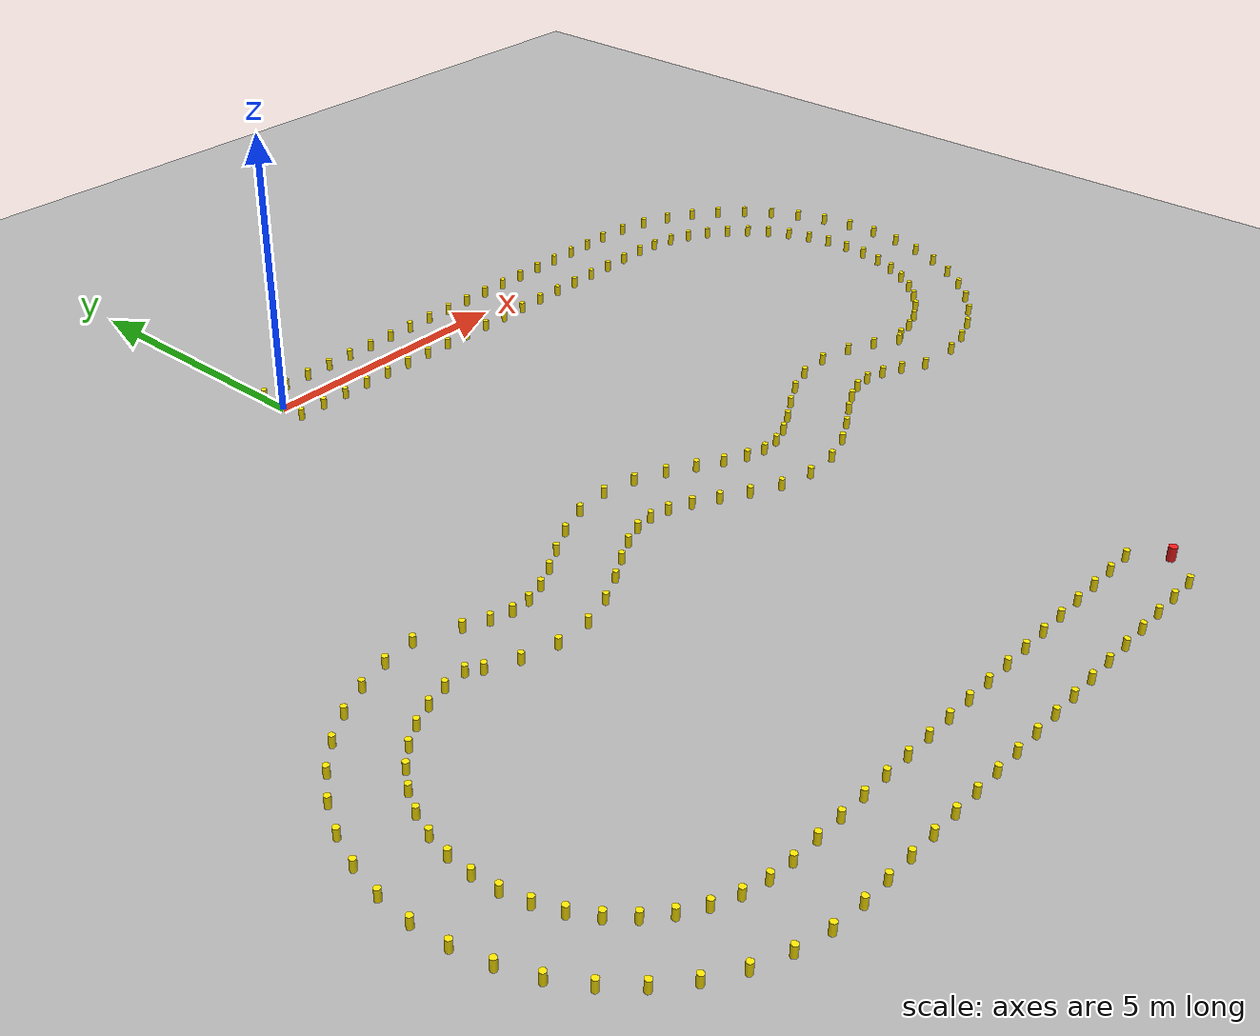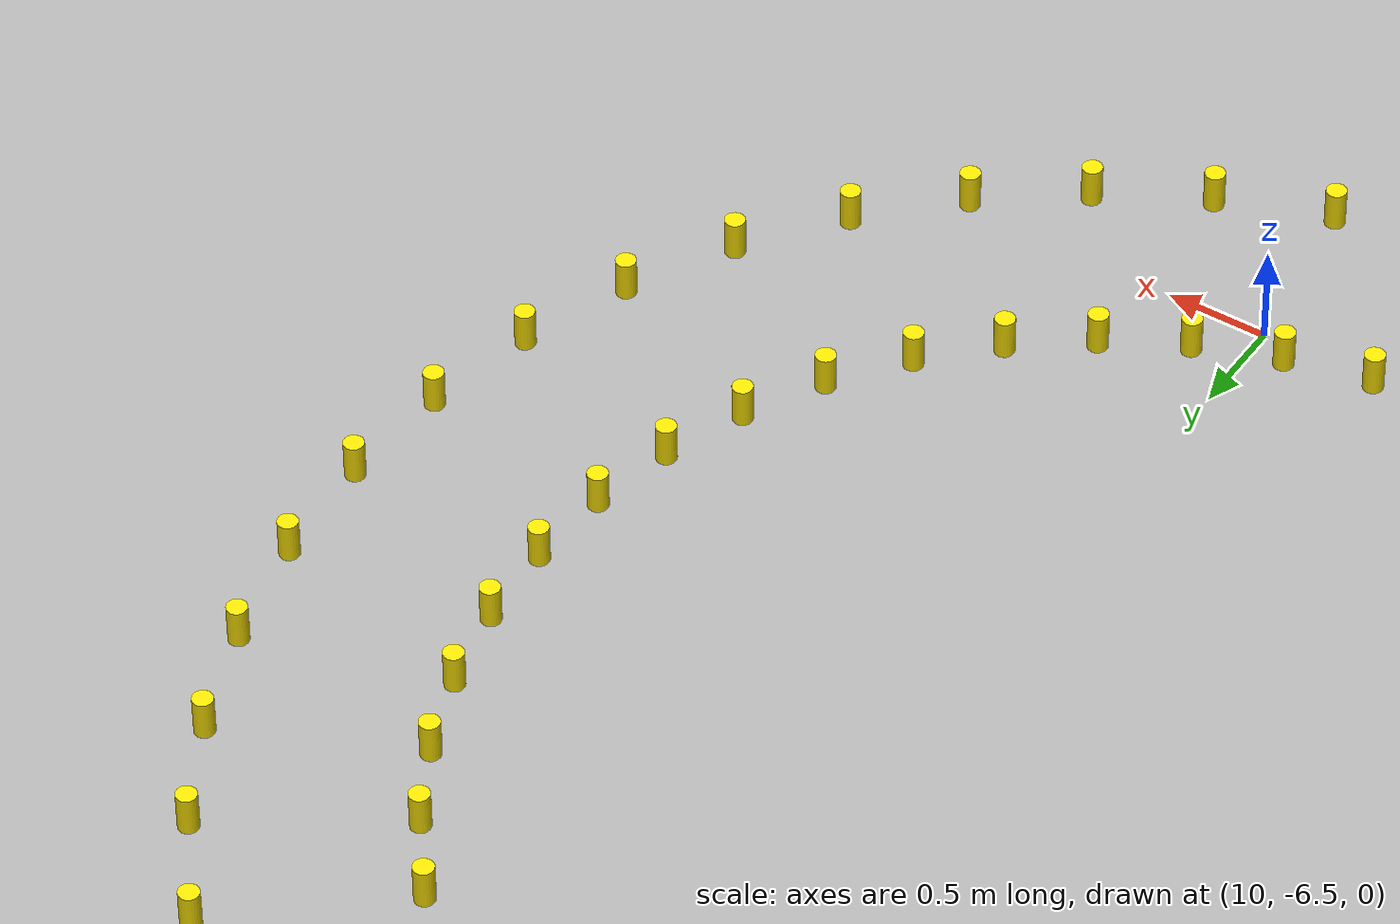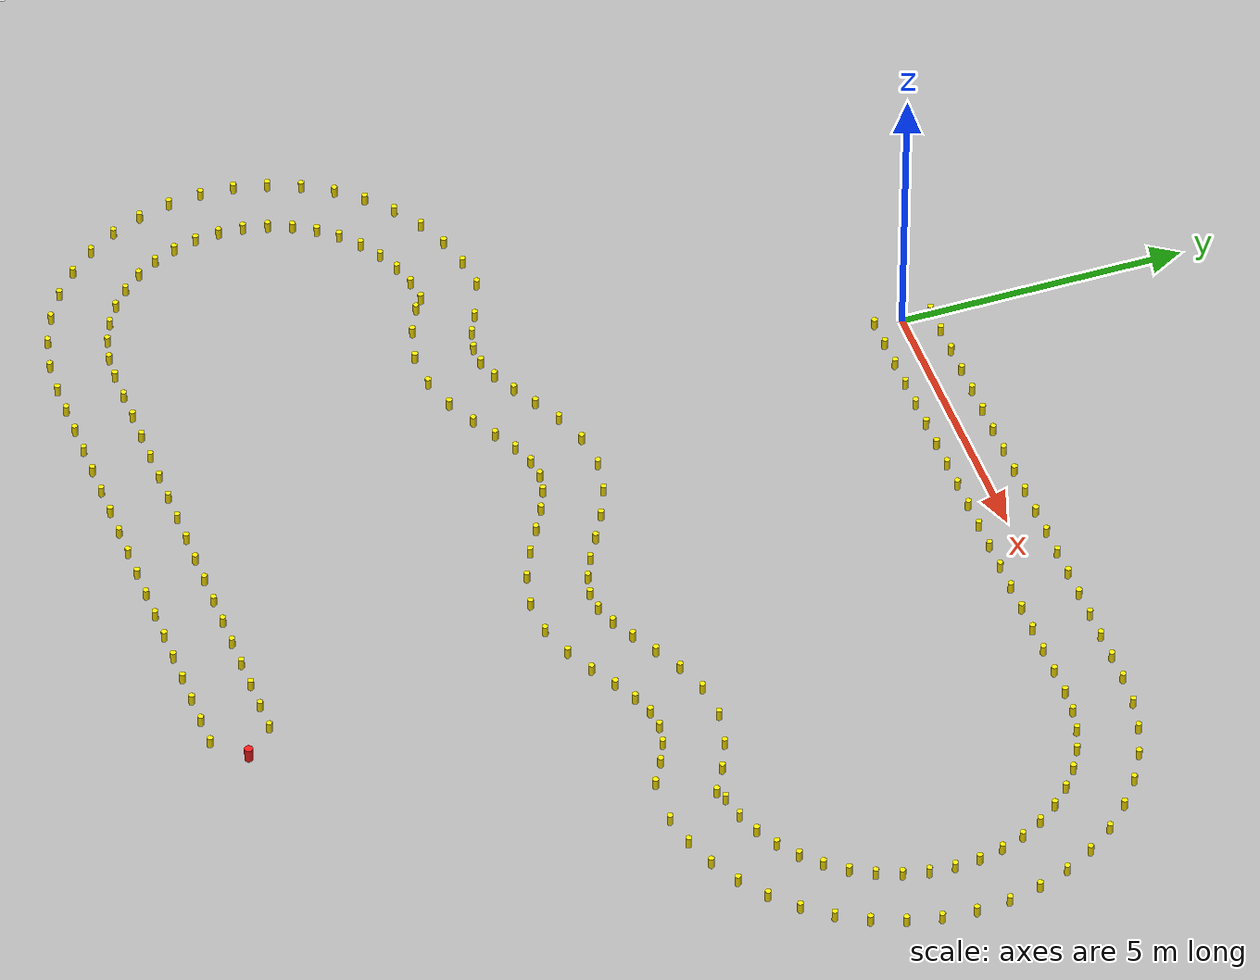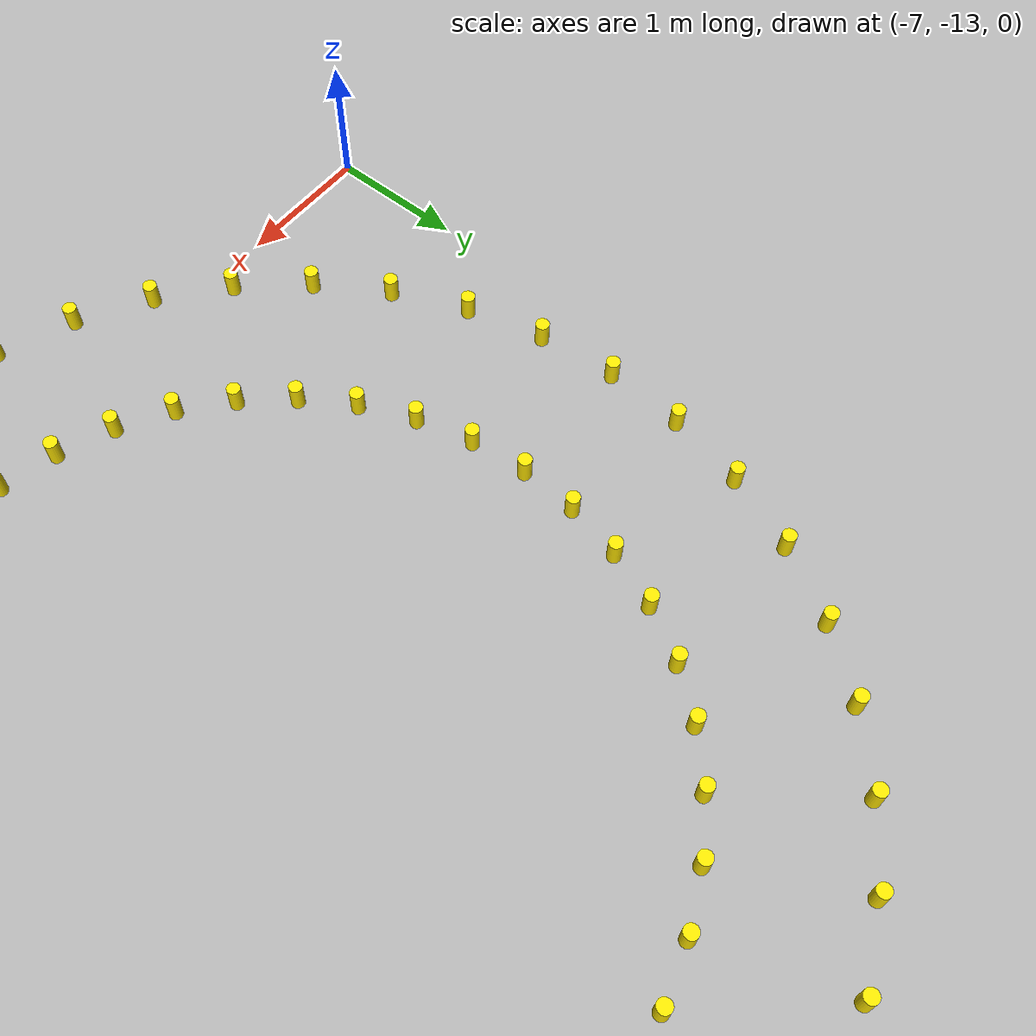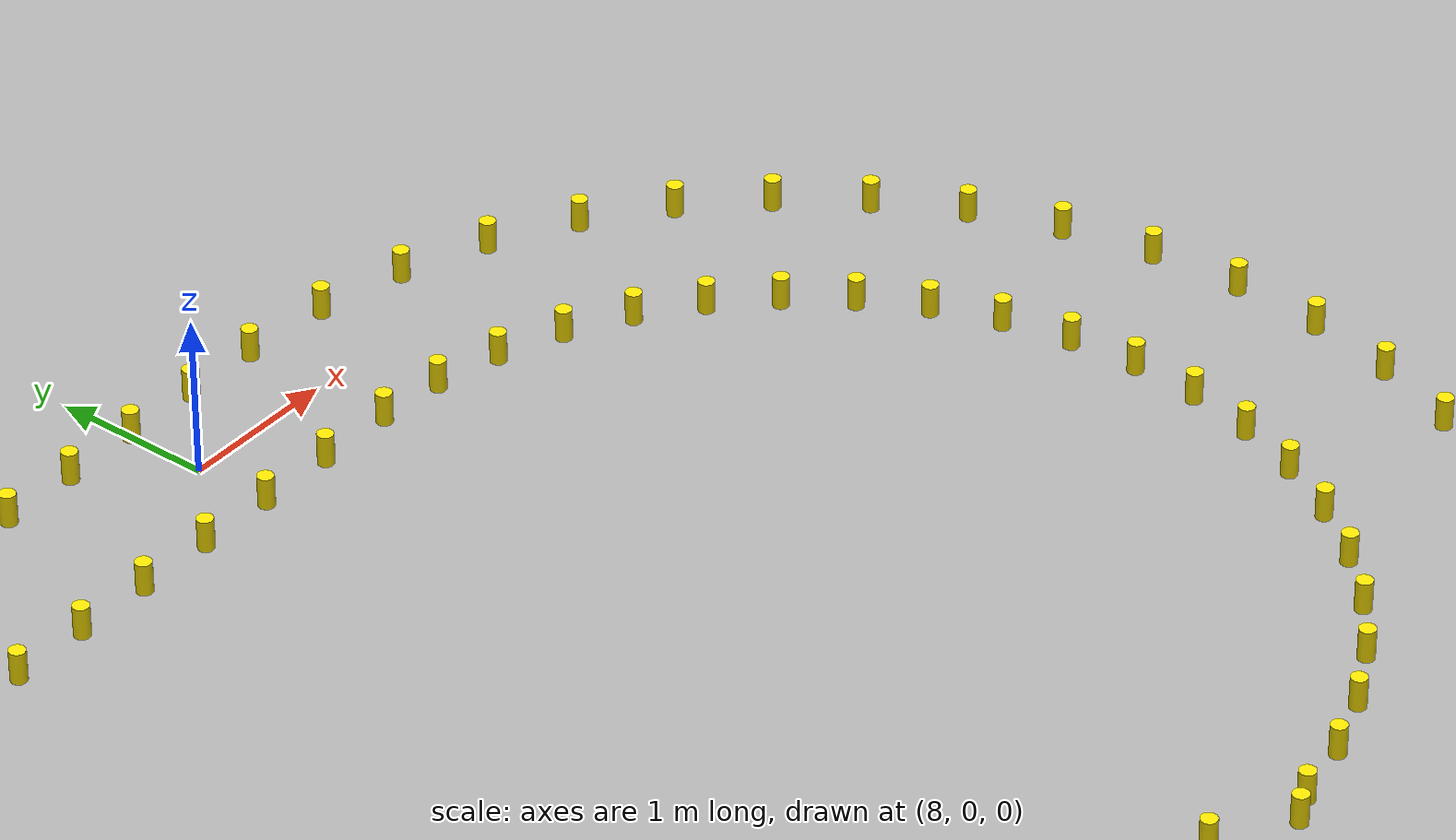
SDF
<?xml version="1.0"?>
<!-- AUTO-GENERATED by scripts/generate_track_cones.py - edit PARAMS there and re-run. -->
<sdf version="1.7">
  <world name="cone_lane">

    <physics type="ode">
      <max_step_size>0.004</max_step_size>
      <real_time_factor>1.0</real_time_factor>
    </physics>

    <plugin filename="libignition-gazebo-physics-system.so"
      name="ignition::gazebo::systems::Physics" />
    <plugin filename="libignition-gazebo-user-commands-system.so"
      name="ignition::gazebo::systems::UserCommands" />
    <plugin filename="libignition-gazebo-scene-broadcaster-system.so"
      name="ignition::gazebo::systems::SceneBroadcaster" />
    <plugin filename="libignition-gazebo-sensors-system.so"
      name="ignition::gazebo::systems::Sensors">
      <render_engine>ogre2</render_engine>
    </plugin>
    <plugin filename="libignition-gazebo-imu-system.so"
      name="ignition::gazebo::systems::Imu" />

    <scene>
      <ambient>0.4 0.4 0.4 1</ambient>
      <background>0.25 0.25 0.25 1</background>
      <shadows>true</shadows>
    </scene>

    <light type="directional" name="sun">
      <cast_shadows>true</cast_shadows>
      <pose>0 0 10 0 0 0</pose>
      <diffuse>0.9 0.9 0.9 1</diffuse>
      <specular>0.3 0.3 0.3 1</specular>
      <attenuation>
        <range>1000</range>
        <constant>0.9</constant>
        <linear>0.01</linear>
        <quadratic>0.001</quadratic>
      </attenuation>
      <direction>-0.5 0.1 -0.9</direction>
    </light>

    <model name="ground_plane">
      <static>true</static>
      <link name="link">
        <collision name="collision">
          <geometry><plane><normal>0 0 1</normal><size>150 150</size></plane></geometry>
          <surface><friction><ode><mu>1.0</mu></ode></friction></surface>
        </collision>
        <visual name="visual">
          <geometry><plane><normal>0 0 1</normal><size>100 100</size></plane></geometry>
          <material>
            <ambient>0.55 0.55 0.55 1</ambient>
            <diffuse>0.70 0.70 0.70 1</diffuse>
            <specular>0.05 0.05 0.05 1</specular>
          </material>
        </visual>
      </link>
    </model>

    <!-- Left yellow cone row -->
    <model name="cone_L001">
      <static>true</static>
      <pose>0.000 0.500 0.1 0 0 0</pose>
      <link name="link">
        <visual name="v">
          <geometry><cylinder><radius>0.05</radius><length>0.2</length></cylinder></geometry>
          <material>
            <ambient>0.9 0.8 0.0 1</ambient>
            <diffuse>1.0 0.9 0.0 1</diffuse>
            <specular>0.2 0.2 0.0 1</specular>
          </material>
        </visual>
        <collision name="c">
          <geometry><cylinder><radius>0.05</radius><length>0.2</length></cylinder></geometry>
        </collision>
      </link>
    </model>
    <model name="cone_L002">
      <static>true</static>
      <pose>0.500 0.500 0.1 0 0 0</pose>
      <link name="link">
        <visual name="v">
          <geometry><cylinder><radius>0.05</radius><length>0.2</length></cylinder></geometry>
          <material>
            <ambient>0.9 0.8 0.0 1</ambient>
            <diffuse>1.0 0.9 0.0 1</diffuse>
            <specular>0.2 0.2 0.0 1</specular>
          </material>
        </visual>
        <collision name="c">
          <geometry><cylinder><radius>0.05</radius><length>0.2</length></cylinder></geometry>
        </collision>
      </link>
    </model>
    <model name="cone_L003">
      <static>true</static>
      <pose>1.000 0.500 0.1 0 0 0</pose>
      <link name="link">
        <visual name="v">
          <geometry><cylinder><radius>0.05</radius><length>0.2</length></cylinder></geometry>
          <material>
            <ambient>0.9 0.8 0.0 1</ambient>
            <diffuse>1.0 0.9 0.0 1</diffuse>
            <specular>0.2 0.2 0.0 1</specular>
          </material>
        </visual>
        <collision name="c">
          <geometry><cylinder><radius>0.05</radius><length>0.2</length></cylinder></geometry>
        </collision>
      </link>
    </model>
    <model name="cone_L004">
      <static>true</static>
      <pose>1.500 0.500 0.1 0 0 0</pose>
      <link name="link">
        <visual name="v">
          <geometry><cylinder><radius>0.05</radius><length>0.2</length></cylinder></geometry>
          <material>
            <ambient>0.9 0.8 0.0 1</ambient>
            <diffuse>1.0 0.9 0.0 1</diffuse>
            <specular>0.2 0.2 0.0 1</specular>
          </material>
        </visual>
        <collision name="c">
          <geometry><cylinder><radius>0.05</radius><length>0.2</length></cylinder></geometry>
        </collision>
      </link>
    </model>
    <model name="cone_L005">
      <static>true</static>
      <pose>2.000 0.500 0.1 0 0 0</pose>
      <link name="link">
        <visual name="v">
          <geometry><cylinder><radius>0.05</radius><length>0.2</length></cylinder></geometry>
          <material>
            <ambient>0.9 0.8 0.0 1</ambient>
            <diffuse>1.0 0.9 0.0 1</diffuse>
            <specular>0.2 0.2 0.0 1</specular>
          </material>
        </visual>
        <collision name="c">
          <geometry><cylinder><radius>0.05</radius><length>0.2</length></cylinder></geometry>
        </collision>
      </link>
    </model>
    <model name="cone_L006">
      <static>true</static>
      <pose>2.500 0.500 0.1 0 0 0</pose>
      <link name="link">
        <visual name="v">
          <geometry><cylinder><radius>0.05</radius><length>0.2</length></cylinder></geometry>
          <material>
            <ambient>0.9 0.8 0.0 1</ambient>
            <diffuse>1.0 0.9 0.0 1</diffuse>
            <specular>0.2 0.2 0.0 1</specular>
          </material>
        </visual>
        <collision name="c">
          <geometry><cylinder><radius>0.05</radius><length>0.2</length></cylinder></geometry>
        </collision>
      </link>
    </model>
    <model name="cone_L007">
      <static>true</static>
      <pose>3.000 0.500 0.1 0 0 0</pose>
      <link name="link">
        <visual name="v">
          <geometry><cylinder><radius>0.05</radius><length>0.2</length></cylinder></geometry>
          <material>
            <ambient>0.9 0.8 0.0 1</ambient>
            <diffuse>1.0 0.9 0.0 1</diffuse>
            <specular>0.2 0.2 0.0 1</specular>
          </material>
        </visual>
        <collision name="c">
          <geometry><cylinder><radius>0.05</radius><length>0.2</length></cylinder></geometry>
        </collision>
      </link>
    </model>
    <model name="cone_L008">
      <static>true</static>
      <pose>3.500 0.500 0.1 0 0 0</pose>
      <link name="link">
        <visual name="v">
          <geometry><cylinder><radius>0.05</radius><length>0.2</length></cylinder></geometry>
          <material>
            <ambient>0.9 0.8 0.0 1</ambient>
            <diffuse>1.0 0.9 0.0 1</diffuse>
            <specular>0.2 0.2 0.0 1</specular>
          </material>
        </visual>
        <collision name="c">
          <geometry><cylinder><radius>0.05</radius><length>0.2</length></cylinder></geometry>
        </collision>
      </link>
    </model>
    <model name="cone_L009">
      <static>true</static>
      <pose>4.000 0.500 0.1 0 0 0</pose>
      <link name="link">
        <visual name="v">
          <geometry><cylinder><radius>0.05</radius><length>0.2</length></cylinder></geometry>
          <material>
            <ambient>0.9 0.8 0.0 1</ambient>
            <diffuse>1.0 0.9 0.0 1</diffuse>
            <specular>0.2 0.2 0.0 1</specular>
          </material>
        </visual>
        <collision name="c">
          <geometry><cylinder><radius>0.05</radius><length>0.2</length></cylinder></geometry>
        </collision>
      </link>
    </model>
    <model name="cone_L010">
      <static>true</static>
      <pose>4.500 0.500 0.1 0 0 0</pose>
      <link name="link">
        <visual name="v">
          <geometry><cylinder><radius>0.05</radius><length>0.2</length></cylinder></geometry>
          <material>
            <ambient>0.9 0.8 0.0 1</ambient>
            <diffuse>1.0 0.9 0.0 1</diffuse>
            <specular>0.2 0.2 0.0 1</specular>
          </material>
        </visual>
        <collision name="c">
          <geometry><cylinder><radius>0.05</radius><length>0.2</length></cylinder></geometry>
        </collision>
      </link>
    </model>
    <model name="cone_L011">
      <static>true</static>
      <pose>5.000 0.500 0.1 0 0 0</pose>
      <link name="link">
        <visual name="v">
          <geometry><cylinder><radius>0.05</radius><length>0.2</length></cylinder></geometry>
          <material>
            <ambient>0.9 0.8 0.0 1</ambient>
            <diffuse>1.0 0.9 0.0 1</diffuse>
            <specular>0.2 0.2 0.0 1</specular>
          </material>
        </visual>
        <collision name="c">
          <geometry><cylinder><radius>0.05</radius><length>0.2</length></cylinder></geometry>
        </collision>
      </link>
    </model>
    <model name="cone_L012">
      <static>true</static>
      <pose>5.500 0.500 0.1 0 0 0</pose>
      <link name="link">
        <visual name="v">
          <geometry><cylinder><radius>0.05</radius><length>0.2</length></cylinder></geometry>
          <material>
            <ambient>0.9 0.8 0.0 1</ambient>
            <diffuse>1.0 0.9 0.0 1</diffuse>
            <specular>0.2 0.2 0.0 1</specular>
          </material>
        </visual>
        <collision name="c">
          <geometry><cylinder><radius>0.05</radius><length>0.2</length></cylinder></geometry>
        </collision>
      </link>
    </model>
    <model name="cone_L013">
      <static>true</static>
      <pose>6.000 0.500 0.1 0 0 0</pose>
      <link name="link">
        <visual name="v">
          <geometry><cylinder><radius>0.05</radius><length>0.2</length></cylinder></geometry>
          <material>
            <ambient>0.9 0.8 0.0 1</ambient>
            <diffuse>1.0 0.9 0.0 1</diffuse>
            <specular>0.2 0.2 0.0 1</specular>
          </material>
        </visual>
        <collision name="c">
          <geometry><cylinder><radius>0.05</radius><length>0.2</length></cylinder></geometry>
        </collision>
      </link>
    </model>
    <model name="cone_L014">
      <static>true</static>
      <pose>6.500 0.500 0.1 0 0 0</pose>
      <link name="link">
        <visual name="v">
          <geometry><cylinder><radius>0.05</radius><length>0.2</length></cylinder></geometry>
          <material>
            <ambient>0.9 0.8 0.0 1</ambient>
            <diffuse>1.0 0.9 0.0 1</diffuse>
            <specular>0.2 0.2 0.0 1</specular>
          </material>
        </visual>
        <collision name="c">
          <geometry><cylinder><radius>0.05</radius><length>0.2</length></cylinder></geometry>
        </collision>
      </link>
    </model>
    <model name="cone_L015">
      <static>true</static>
      <pose>7.000 0.500 0.1 0 0 0</pose>
      <link name="link">
        <visual name="v">
          <geometry><cylinder><radius>0.05</radius><length>0.2</length></cylinder></geometry>
          <material>
            <ambient>0.9 0.8 0.0 1</ambient>
            <diffuse>1.0 0.9 0.0 1</diffuse>
            <specular>0.2 0.2 0.0 1</specular>
          </material>
        </visual>
        <collision name="c">
          <geometry><cylinder><radius>0.05</radius><length>0.2</length></cylinder></geometry>
        </collision>
      </link>
    </model>
    <model name="cone_L016">
      <static>true</static>
      <pose>7.500 0.500 0.1 0 0 0</pose>
      <link name="link">
        <visual name="v">
          <geometry><cylinder><radius>0.05</radius><length>0.2</length></cylinder></geometry>
          <material>
            <ambient>0.9 0.8 0.0 1</ambient>
            <diffuse>1.0 0.9 0.0 1</diffuse>
            <specular>0.2 0.2 0.0 1</specular>
          </material>
        </visual>
        <collision name="c">
          <geometry><cylinder><radius>0.05</radius><length>0.2</length></cylinder></geometry>
        </collision>
      </link>
    </model>
    <model name="cone_L017">
      <static>true</static>
      <pose>8.000 0.500 0.1 0 0 0</pose>
      <link name="link">
        <visual name="v">
          <geometry><cylinder><radius>0.05</radius><length>0.2</length></cylinder></geometry>
          <material>
            <ambient>0.9 0.8 0.0 1</ambient>
            <diffuse>1.0 0.9 0.0 1</diffuse>
            <specular>0.2 0.2 0.0 1</specular>
          </material>
        </visual>
        <collision name="c">
          <geometry><cylinder><radius>0.05</radius><length>0.2</length></cylinder></geometry>
        </collision>
      </link>
    </model>
    <model name="cone_L018">
      <static>true</static>
      <pose>8.500 0.500 0.1 0 0 0</pose>
      <link name="link">
        <visual name="v">
          <geometry><cylinder><radius>0.05</radius><length>0.2</length></cylinder></geometry>
          <material>
            <ambient>0.9 0.8 0.0 1</ambient>
            <diffuse>1.0 0.9 0.0 1</diffuse>
            <specular>0.2 0.2 0.0 1</specular>
          </material>
        </visual>
        <collision name="c">
          <geometry><cylinder><radius>0.05</radius><length>0.2</length></cylinder></geometry>
        </collision>
      </link>
    </model>
    <model name="cone_L019">
      <static>true</static>
      <pose>9.001 0.500 0.1 0 0 0</pose>
      <link name="link">
        <visual name="v">
          <geometry><cylinder><radius>0.05</radius><length>0.2</length></cylinder></geometry>
          <material>
            <ambient>0.9 0.8 0.0 1</ambient>
            <diffuse>1.0 0.9 0.0 1</diffuse>
            <specular>0.2 0.2 0.0 1</specular>
          </material>
        </visual>
        <collision name="c">
          <geometry><cylinder><radius>0.05</radius><length>0.2</length></cylinder></geometry>
        </collision>
      </link>
    </model>
    <model name="cone_L020">
      <static>true</static>
      <pose>9.570 0.459 0.1 0 0 0</pose>
      <link name="link">
        <visual name="v">
          <geometry><cylinder><radius>0.05</radius><length>0.2</length></cylinder></geometry>
          <material>
            <ambient>0.9 0.8 0.0 1</ambient>
            <diffuse>1.0 0.9 0.0 1</diffuse>
            <specular>0.2 0.2 0.0 1</specular>
          </material>
        </visual>
        <collision name="c">
          <geometry><cylinder><radius>0.05</radius><length>0.2</length></cylinder></geometry>
        </collision>
      </link>
    </model>
    <model name="cone_L021">
      <static>true</static>
      <pose>10.129 0.337 0.1 0 0 0</pose>
      <link name="link">
        <visual name="v">
          <geometry><cylinder><radius>0.05</radius><length>0.2</length></cylinder></geometry>
          <material>
            <ambient>0.9 0.8 0.0 1</ambient>
            <diffuse>1.0 0.9 0.0 1</diffuse>
            <specular>0.2 0.2 0.0 1</specular>
          </material>
        </visual>
        <collision name="c">
          <geometry><cylinder><radius>0.05</radius><length>0.2</length></cylinder></geometry>
        </collision>
      </link>
    </model>
    <model name="cone_L022">
      <static>true</static>
      <pose>10.664 0.137 0.1 0 0 0</pose>
      <link name="link">
        <visual name="v">
          <geometry><cylinder><radius>0.05</radius><length>0.2</length></cylinder></geometry>
          <material>
            <ambient>0.9 0.8 0.0 1</ambient>
            <diffuse>1.0 0.9 0.0 1</diffuse>
            <specular>0.2 0.2 0.0 1</specular>
          </material>
        </visual>
        <collision name="c">
          <geometry><cylinder><radius>0.05</radius><length>0.2</length></cylinder></geometry>
        </collision>
      </link>
    </model>
    <model name="cone_L023">
      <static>true</static>
      <pose>11.166 -0.137 0.1 0 0 0</pose>
      <link name="link">
        <visual name="v">
          <geometry><cylinder><radius>0.05</radius><length>0.2</length></cylinder></geometry>
          <material>
            <ambient>0.9 0.8 0.0 1</ambient>
            <diffuse>1.0 0.9 0.0 1</diffuse>
            <specular>0.2 0.2 0.0 1</specular>
          </material>
        </visual>
        <collision name="c">
          <geometry><cylinder><radius>0.05</radius><length>0.2</length></cylinder></geometry>
        </collision>
      </link>
    </model>
    <model name="cone_L024">
      <static>true</static>
      <pose>11.623 -0.480 0.1 0 0 0</pose>
      <link name="link">
        <visual name="v">
          <geometry><cylinder><radius>0.05</radius><length>0.2</length></cylinder></geometry>
          <material>
            <ambient>0.9 0.8 0.0 1</ambient>
            <diffuse>1.0 0.9 0.0 1</diffuse>
            <specular>0.2 0.2 0.0 1</specular>
          </material>
        </visual>
        <collision name="c">
          <geometry><cylinder><radius>0.05</radius><length>0.2</length></cylinder></geometry>
        </collision>
      </link>
    </model>
    <model name="cone_L025">
      <static>true</static>
      <pose>12.027 -0.885 0.1 0 0 0</pose>
      <link name="link">
        <visual name="v">
          <geometry><cylinder><radius>0.05</radius><length>0.2</length></cylinder></geometry>
          <material>
            <ambient>0.9 0.8 0.0 1</ambient>
            <diffuse>1.0 0.9 0.0 1</diffuse>
            <specular>0.2 0.2 0.0 1</specular>
          </material>
        </visual>
        <collision name="c">
          <geometry><cylinder><radius>0.05</radius><length>0.2</length></cylinder></geometry>
        </collision>
      </link>
    </model>
    <model name="cone_L026">
      <static>true</static>
      <pose>12.369 -1.344 0.1 0 0 0</pose>
      <link name="link">
        <visual name="v">
          <geometry><cylinder><radius>0.05</radius><length>0.2</length></cylinder></geometry>
          <material>
            <ambient>0.9 0.8 0.0 1</ambient>
            <diffuse>1.0 0.9 0.0 1</diffuse>
            <specular>0.2 0.2 0.0 1</specular>
          </material>
        </visual>
        <collision name="c">
          <geometry><cylinder><radius>0.05</radius><length>0.2</length></cylinder></geometry>
        </collision>
      </link>
    </model>
    <model name="cone_L027">
      <static>true</static>
      <pose>12.642 -1.846 0.1 0 0 0</pose>
      <link name="link">
        <visual name="v">
          <geometry><cylinder><radius>0.05</radius><length>0.2</length></cylinder></geometry>
          <material>
            <ambient>0.9 0.8 0.0 1</ambient>
            <diffuse>1.0 0.9 0.0 1</diffuse>
            <specular>0.2 0.2 0.0 1</specular>
          </material>
        </visual>
        <collision name="c">
          <geometry><cylinder><radius>0.05</radius><length>0.2</length></cylinder></geometry>
        </collision>
      </link>
    </model>
    <model name="cone_L028">
      <static>true</static>
      <pose>12.841 -2.382 0.1 0 0 0</pose>
      <link name="link">
        <visual name="v">
          <geometry><cylinder><radius>0.05</radius><length>0.2</length></cylinder></geometry>
          <material>
            <ambient>0.9 0.8 0.0 1</ambient>
            <diffuse>1.0 0.9 0.0 1</diffuse>
            <specular>0.2 0.2 0.0 1</specular>
          </material>
        </visual>
        <collision name="c">
          <geometry><cylinder><radius>0.05</radius><length>0.2</length></cylinder></geometry>
        </collision>
      </link>
    </model>
    <model name="cone_L029">
      <static>true</static>
      <pose>12.961 -2.941 0.1 0 0 0</pose>
      <link name="link">
        <visual name="v">
          <geometry><cylinder><radius>0.05</radius><length>0.2</length></cylinder></geometry>
          <material>
            <ambient>0.9 0.8 0.0 1</ambient>
            <diffuse>1.0 0.9 0.0 1</diffuse>
            <specular>0.2 0.2 0.0 1</specular>
          </material>
        </visual>
        <collision name="c">
          <geometry><cylinder><radius>0.05</radius><length>0.2</length></cylinder></geometry>
        </collision>
      </link>
    </model>
    <model name="cone_L030">
      <static>true</static>
      <pose>13.000 -3.511 0.1 0 0 0</pose>
      <link name="link">
        <visual name="v">
          <geometry><cylinder><radius>0.05</radius><length>0.2</length></cylinder></geometry>
          <material>
            <ambient>0.9 0.8 0.0 1</ambient>
            <diffuse>1.0 0.9 0.0 1</diffuse>
            <specular>0.2 0.2 0.0 1</specular>
          </material>
        </visual>
        <collision name="c">
          <geometry><cylinder><radius>0.05</radius><length>0.2</length></cylinder></geometry>
        </collision>
      </link>
    </model>
    <model name="cone_L031">
      <static>true</static>
      <pose>12.957 -4.082 0.1 0 0 0</pose>
      <link name="link">
        <visual name="v">
          <geometry><cylinder><radius>0.05</radius><length>0.2</length></cylinder></geometry>
          <material>
            <ambient>0.9 0.8 0.0 1</ambient>
            <diffuse>1.0 0.9 0.0 1</diffuse>
            <specular>0.2 0.2 0.0 1</specular>
          </material>
        </visual>
        <collision name="c">
          <geometry><cylinder><radius>0.05</radius><length>0.2</length></cylinder></geometry>
        </collision>
      </link>
    </model>
    <model name="cone_L032">
      <static>true</static>
      <pose>12.834 -4.640 0.1 0 0 0</pose>
      <link name="link">
        <visual name="v">
          <geometry><cylinder><radius>0.05</radius><length>0.2</length></cylinder></geometry>
          <material>
            <ambient>0.9 0.8 0.0 1</ambient>
            <diffuse>1.0 0.9 0.0 1</diffuse>
            <specular>0.2 0.2 0.0 1</specular>
          </material>
        </visual>
        <collision name="c">
          <geometry><cylinder><radius>0.05</radius><length>0.2</length></cylinder></geometry>
        </collision>
      </link>
    </model>
    <model name="cone_L033">
      <static>true</static>
      <pose>12.632 -5.175 0.1 0 0 0</pose>
      <link name="link">
        <visual name="v">
          <geometry><cylinder><radius>0.05</radius><length>0.2</length></cylinder></geometry>
          <material>
            <ambient>0.9 0.8 0.0 1</ambient>
            <diffuse>1.0 0.9 0.0 1</diffuse>
            <specular>0.2 0.2 0.0 1</specular>
          </material>
        </visual>
        <collision name="c">
          <geometry><cylinder><radius>0.05</radius><length>0.2</length></cylinder></geometry>
        </collision>
      </link>
    </model>
    <model name="cone_L034">
      <static>true</static>
      <pose>12.357 -5.676 0.1 0 0 0</pose>
      <link name="link">
        <visual name="v">
          <geometry><cylinder><radius>0.05</radius><length>0.2</length></cylinder></geometry>
          <material>
            <ambient>0.9 0.8 0.0 1</ambient>
            <diffuse>1.0 0.9 0.0 1</diffuse>
            <specular>0.2 0.2 0.0 1</specular>
          </material>
        </visual>
        <collision name="c">
          <geometry><cylinder><radius>0.05</radius><length>0.2</length></cylinder></geometry>
        </collision>
      </link>
    </model>
    <model name="cone_L035">
      <static>true</static>
      <pose>12.012 -6.132 0.1 0 0 0</pose>
      <link name="link">
        <visual name="v">
          <geometry><cylinder><radius>0.05</radius><length>0.2</length></cylinder></geometry>
          <material>
            <ambient>0.9 0.8 0.0 1</ambient>
            <diffuse>1.0 0.9 0.0 1</diffuse>
            <specular>0.2 0.2 0.0 1</specular>
          </material>
        </visual>
        <collision name="c">
          <geometry><cylinder><radius>0.05</radius><length>0.2</length></cylinder></geometry>
        </collision>
      </link>
    </model>
    <model name="cone_L036">
      <static>true</static>
      <pose>11.606 -6.535 0.1 0 0 0</pose>
      <link name="link">
        <visual name="v">
          <geometry><cylinder><radius>0.05</radius><length>0.2</length></cylinder></geometry>
          <material>
            <ambient>0.9 0.8 0.0 1</ambient>
            <diffuse>1.0 0.9 0.0 1</diffuse>
            <specular>0.2 0.2 0.0 1</specular>
          </material>
        </visual>
        <collision name="c">
          <geometry><cylinder><radius>0.05</radius><length>0.2</length></cylinder></geometry>
        </collision>
      </link>
    </model>
    <model name="cone_L037">
      <static>true</static>
      <pose>11.147 -6.875 0.1 0 0 0</pose>
      <link name="link">
        <visual name="v">
          <geometry><cylinder><radius>0.05</radius><length>0.2</length></cylinder></geometry>
          <material>
            <ambient>0.9 0.8 0.0 1</ambient>
            <diffuse>1.0 0.9 0.0 1</diffuse>
            <specular>0.2 0.2 0.0 1</specular>
          </material>
        </visual>
        <collision name="c">
          <geometry><cylinder><radius>0.05</radius><length>0.2</length></cylinder></geometry>
        </collision>
      </link>
    </model>
    <model name="cone_L038">
      <static>true</static>
      <pose>10.644 -7.147 0.1 0 0 0</pose>
      <link name="link">
        <visual name="v">
          <geometry><cylinder><radius>0.05</radius><length>0.2</length></cylinder></geometry>
          <material>
            <ambient>0.9 0.8 0.0 1</ambient>
            <diffuse>1.0 0.9 0.0 1</diffuse>
            <specular>0.2 0.2 0.0 1</specular>
          </material>
        </visual>
        <collision name="c">
          <geometry><cylinder><radius>0.05</radius><length>0.2</length></cylinder></geometry>
        </collision>
      </link>
    </model>
    <model name="cone_L039">
      <static>true</static>
      <pose>10.107 -7.344 0.1 0 0 0</pose>
      <link name="link">
        <visual name="v">
          <geometry><cylinder><radius>0.05</radius><length>0.2</length></cylinder></geometry>
          <material>
            <ambient>0.9 0.8 0.0 1</ambient>
            <diffuse>1.0 0.9 0.0 1</diffuse>
            <specular>0.2 0.2 0.0 1</specular>
          </material>
        </visual>
        <collision name="c">
          <geometry><cylinder><radius>0.05</radius><length>0.2</length></cylinder></geometry>
        </collision>
      </link>
    </model>
    <model name="cone_L040">
      <static>true</static>
      <pose>9.548 -7.462 0.1 0 0 0</pose>
      <link name="link">
        <visual name="v">
          <geometry><cylinder><radius>0.05</radius><length>0.2</length></cylinder></geometry>
          <material>
            <ambient>0.9 0.8 0.0 1</ambient>
            <diffuse>1.0 0.9 0.0 1</diffuse>
            <specular>0.2 0.2 0.0 1</specular>
          </material>
        </visual>
        <collision name="c">
          <geometry><cylinder><radius>0.05</radius><length>0.2</length></cylinder></geometry>
        </collision>
      </link>
    </model>
    <model name="cone_L041">
      <static>true</static>
      <pose>8.731 -7.422 0.1 0 0 0</pose>
      <link name="link">
        <visual name="v">
          <geometry><cylinder><radius>0.05</radius><length>0.2</length></cylinder></geometry>
          <material>
            <ambient>0.9 0.8 0.0 1</ambient>
            <diffuse>1.0 0.9 0.0 1</diffuse>
            <specular>0.2 0.2 0.0 1</specular>
          </material>
        </visual>
        <collision name="c">
          <geometry><cylinder><radius>0.05</radius><length>0.2</length></cylinder></geometry>
        </collision>
      </link>
    </model>
    <model name="cone_L042">
      <static>true</static>
      <pose>8.313 -7.191 0.1 0 0 0</pose>
      <link name="link">
        <visual name="v">
          <geometry><cylinder><radius>0.05</radius><length>0.2</length></cylinder></geometry>
          <material>
            <ambient>0.9 0.8 0.0 1</ambient>
            <diffuse>1.0 0.9 0.0 1</diffuse>
            <specular>0.2 0.2 0.0 1</specular>
          </material>
        </visual>
        <collision name="c">
          <geometry><cylinder><radius>0.05</radius><length>0.2</length></cylinder></geometry>
        </collision>
      </link>
    </model>
    <model name="cone_L043">
      <static>true</static>
      <pose>7.940 -7.029 0.1 0 0 0</pose>
      <link name="link">
        <visual name="v">
          <geometry><cylinder><radius>0.05</radius><length>0.2</length></cylinder></geometry>
          <material>
            <ambient>0.9 0.8 0.0 1</ambient>
            <diffuse>1.0 0.9 0.0 1</diffuse>
            <specular>0.2 0.2 0.0 1</specular>
          </material>
        </visual>
        <collision name="c">
          <geometry><cylinder><radius>0.05</radius><length>0.2</length></cylinder></geometry>
        </collision>
      </link>
    </model>
    <model name="cone_L044">
      <static>true</static>
      <pose>7.570 -6.952 0.1 0 0 0</pose>
      <link name="link">
        <visual name="v">
          <geometry><cylinder><radius>0.05</radius><length>0.2</length></cylinder></geometry>
          <material>
            <ambient>0.9 0.8 0.0 1</ambient>
            <diffuse>1.0 0.9 0.0 1</diffuse>
            <specular>0.2 0.2 0.0 1</specular>
          </material>
        </visual>
        <collision name="c">
          <geometry><cylinder><radius>0.05</radius><length>0.2</length></cylinder></geometry>
        </collision>
      </link>
    </model>
    <model name="cone_L045">
      <static>true</static>
      <pose>7.214 -6.984 0.1 0 0 0</pose>
      <link name="link">
        <visual name="v">
          <geometry><cylinder><radius>0.05</radius><length>0.2</length></cylinder></geometry>
          <material>
            <ambient>0.9 0.8 0.0 1</ambient>
            <diffuse>1.0 0.9 0.0 1</diffuse>
            <specular>0.2 0.2 0.0 1</specular>
          </material>
        </visual>
        <collision name="c">
          <geometry><cylinder><radius>0.05</radius><length>0.2</length></cylinder></geometry>
        </collision>
      </link>
    </model>
    <model name="cone_L046">
      <static>true</static>
      <pose>6.846 -7.114 0.1 0 0 0</pose>
      <link name="link">
        <visual name="v">
          <geometry><cylinder><radius>0.05</radius><length>0.2</length></cylinder></geometry>
          <material>
            <ambient>0.9 0.8 0.0 1</ambient>
            <diffuse>1.0 0.9 0.0 1</diffuse>
            <specular>0.2 0.2 0.0 1</specular>
          </material>
        </visual>
        <collision name="c">
          <geometry><cylinder><radius>0.05</radius><length>0.2</length></cylinder></geometry>
        </collision>
      </link>
    </model>
    <model name="cone_L047">
      <static>true</static>
      <pose>6.445 -7.321 0.1 0 0 0</pose>
      <link name="link">
        <visual name="v">
          <geometry><cylinder><radius>0.05</radius><length>0.2</length></cylinder></geometry>
          <material>
            <ambient>0.9 0.8 0.0 1</ambient>
            <diffuse>1.0 0.9 0.0 1</diffuse>
            <specular>0.2 0.2 0.0 1</specular>
          </material>
        </visual>
        <collision name="c">
          <geometry><cylinder><radius>0.05</radius><length>0.2</length></cylinder></geometry>
        </collision>
      </link>
    </model>
    <model name="cone_L048">
      <static>true</static>
      <pose>6.004 -7.573 0.1 0 0 0</pose>
      <link name="link">
        <visual name="v">
          <geometry><cylinder><radius>0.05</radius><length>0.2</length></cylinder></geometry>
          <material>
            <ambient>0.9 0.8 0.0 1</ambient>
            <diffuse>1.0 0.9 0.0 1</diffuse>
            <specular>0.2 0.2 0.0 1</specular>
          </material>
        </visual>
        <collision name="c">
          <geometry><cylinder><radius>0.05</radius><length>0.2</length></cylinder></geometry>
        </collision>
      </link>
    </model>
    <model name="cone_L049">
      <static>true</static>
      <pose>5.520 -7.818 0.1 0 0 0</pose>
      <link name="link">
        <visual name="v">
          <geometry><cylinder><radius>0.05</radius><length>0.2</length></cylinder></geometry>
          <material>
            <ambient>0.9 0.8 0.0 1</ambient>
            <diffuse>1.0 0.9 0.0 1</diffuse>
            <specular>0.2 0.2 0.0 1</specular>
          </material>
        </visual>
        <collision name="c">
          <geometry><cylinder><radius>0.05</radius><length>0.2</length></cylinder></geometry>
        </collision>
      </link>
    </model>
    <model name="cone_L050">
      <static>true</static>
      <pose>4.938 -8.006 0.1 0 0 0</pose>
      <link name="link">
        <visual name="v">
          <geometry><cylinder><radius>0.05</radius><length>0.2</length></cylinder></geometry>
          <material>
            <ambient>0.9 0.8 0.0 1</ambient>
            <diffuse>1.0 0.9 0.0 1</diffuse>
            <specular>0.2 0.2 0.0 1</specular>
          </material>
        </visual>
        <collision name="c">
          <geometry><cylinder><radius>0.05</radius><length>0.2</length></cylinder></geometry>
        </collision>
      </link>
    </model>
    <model name="cone_L051">
      <static>true</static>
      <pose>4.292 -8.040 0.1 0 0 0</pose>
      <link name="link">
        <visual name="v">
          <geometry><cylinder><radius>0.05</radius><length>0.2</length></cylinder></geometry>
          <material>
            <ambient>0.9 0.8 0.0 1</ambient>
            <diffuse>1.0 0.9 0.0 1</diffuse>
            <specular>0.2 0.2 0.0 1</specular>
          </material>
        </visual>
        <collision name="c">
          <geometry><cylinder><radius>0.05</radius><length>0.2</length></cylinder></geometry>
        </collision>
      </link>
    </model>
    <model name="cone_L052">
      <static>true</static>
      <pose>3.692 -7.902 0.1 0 0 0</pose>
      <link name="link">
        <visual name="v">
          <geometry><cylinder><radius>0.05</radius><length>0.2</length></cylinder></geometry>
          <material>
            <ambient>0.9 0.8 0.0 1</ambient>
            <diffuse>1.0 0.9 0.0 1</diffuse>
            <specular>0.2 0.2 0.0 1</specular>
          </material>
        </visual>
        <collision name="c">
          <geometry><cylinder><radius>0.05</radius><length>0.2</length></cylinder></geometry>
        </collision>
      </link>
    </model>
    <model name="cone_L053">
      <static>true</static>
      <pose>3.167 -7.666 0.1 0 0 0</pose>
      <link name="link">
        <visual name="v">
          <geometry><cylinder><radius>0.05</radius><length>0.2</length></cylinder></geometry>
          <material>
            <ambient>0.9 0.8 0.0 1</ambient>
            <diffuse>1.0 0.9 0.0 1</diffuse>
            <specular>0.2 0.2 0.0 1</specular>
          </material>
        </visual>
        <collision name="c">
          <geometry><cylinder><radius>0.05</radius><length>0.2</length></cylinder></geometry>
        </collision>
      </link>
    </model>
    <model name="cone_L054">
      <static>true</static>
      <pose>2.711 -7.410 0.1 0 0 0</pose>
      <link name="link">
        <visual name="v">
          <geometry><cylinder><radius>0.05</radius><length>0.2</length></cylinder></geometry>
          <material>
            <ambient>0.9 0.8 0.0 1</ambient>
            <diffuse>1.0 0.9 0.0 1</diffuse>
            <specular>0.2 0.2 0.0 1</specular>
          </material>
        </visual>
        <collision name="c">
          <geometry><cylinder><radius>0.05</radius><length>0.2</length></cylinder></geometry>
        </collision>
      </link>
    </model>
    <model name="cone_L055">
      <static>true</static>
      <pose>2.295 -7.181 0.1 0 0 0</pose>
      <link name="link">
        <visual name="v">
          <geometry><cylinder><radius>0.05</radius><length>0.2</length></cylinder></geometry>
          <material>
            <ambient>0.9 0.8 0.0 1</ambient>
            <diffuse>1.0 0.9 0.0 1</diffuse>
            <specular>0.2 0.2 0.0 1</specular>
          </material>
        </visual>
        <collision name="c">
          <geometry><cylinder><radius>0.05</radius><length>0.2</length></cylinder></geometry>
        </collision>
      </link>
    </model>
    <model name="cone_L056">
      <static>true</static>
      <pose>1.908 -7.018 0.1 0 0 0</pose>
      <link name="link">
        <visual name="v">
          <geometry><cylinder><radius>0.05</radius><length>0.2</length></cylinder></geometry>
          <material>
            <ambient>0.9 0.8 0.0 1</ambient>
            <diffuse>1.0 0.9 0.0 1</diffuse>
            <specular>0.2 0.2 0.0 1</specular>
          </material>
        </visual>
        <collision name="c">
          <geometry><cylinder><radius>0.05</radius><length>0.2</length></cylinder></geometry>
        </collision>
      </link>
    </model>
    <model name="cone_L057">
      <static>true</static>
      <pose>1.556 -6.951 0.1 0 0 0</pose>
      <link name="link">
        <visual name="v">
          <geometry><cylinder><radius>0.05</radius><length>0.2</length></cylinder></geometry>
          <material>
            <ambient>0.9 0.8 0.0 1</ambient>
            <diffuse>1.0 0.9 0.0 1</diffuse>
            <specular>0.2 0.2 0.0 1</specular>
          </material>
        </visual>
        <collision name="c">
          <geometry><cylinder><radius>0.05</radius><length>0.2</length></cylinder></geometry>
        </collision>
      </link>
    </model>
    <model name="cone_L058">
      <static>true</static>
      <pose>1.199 -6.988 0.1 0 0 0</pose>
      <link name="link">
        <visual name="v">
          <geometry><cylinder><radius>0.05</radius><length>0.2</length></cylinder></geometry>
          <material>
            <ambient>0.9 0.8 0.0 1</ambient>
            <diffuse>1.0 0.9 0.0 1</diffuse>
            <specular>0.2 0.2 0.0 1</specular>
          </material>
        </visual>
        <collision name="c">
          <geometry><cylinder><radius>0.05</radius><length>0.2</length></cylinder></geometry>
        </collision>
      </link>
    </model>
    <model name="cone_L059">
      <static>true</static>
      <pose>0.811 -7.130 0.1 0 0 0</pose>
      <link name="link">
        <visual name="v">
          <geometry><cylinder><radius>0.05</radius><length>0.2</length></cylinder></geometry>
          <material>
            <ambient>0.9 0.8 0.0 1</ambient>
            <diffuse>1.0 0.9 0.0 1</diffuse>
            <specular>0.2 0.2 0.0 1</specular>
          </material>
        </visual>
        <collision name="c">
          <geometry><cylinder><radius>0.05</radius><length>0.2</length></cylinder></geometry>
        </collision>
      </link>
    </model>
    <model name="cone_L060">
      <static>true</static>
      <pose>0.407 -7.343 0.1 0 0 0</pose>
      <link name="link">
        <visual name="v">
          <geometry><cylinder><radius>0.05</radius><length>0.2</length></cylinder></geometry>
          <material>
            <ambient>0.9 0.8 0.0 1</ambient>
            <diffuse>1.0 0.9 0.0 1</diffuse>
            <specular>0.2 0.2 0.0 1</specular>
          </material>
        </visual>
        <collision name="c">
          <geometry><cylinder><radius>0.05</radius><length>0.2</length></cylinder></geometry>
        </collision>
      </link>
    </model>
    <model name="cone_L061">
      <static>true</static>
      <pose>-0.017 -7.585 0.1 0 0 0</pose>
      <link name="link">
        <visual name="v">
          <geometry><cylinder><radius>0.05</radius><length>0.2</length></cylinder></geometry>
          <material>
            <ambient>0.9 0.8 0.0 1</ambient>
            <diffuse>1.0 0.9 0.0 1</diffuse>
            <specular>0.2 0.2 0.0 1</specular>
          </material>
        </visual>
        <collision name="c">
          <geometry><cylinder><radius>0.05</radius><length>0.2</length></cylinder></geometry>
        </collision>
      </link>
    </model>
    <model name="cone_L062">
      <static>true</static>
      <pose>-0.526 -7.838 0.1 0 0 0</pose>
      <link name="link">
        <visual name="v">
          <geometry><cylinder><radius>0.05</radius><length>0.2</length></cylinder></geometry>
          <material>
            <ambient>0.9 0.8 0.0 1</ambient>
            <diffuse>1.0 0.9 0.0 1</diffuse>
            <specular>0.2 0.2 0.0 1</specular>
          </material>
        </visual>
        <collision name="c">
          <geometry><cylinder><radius>0.05</radius><length>0.2</length></cylinder></geometry>
        </collision>
      </link>
    </model>
    <model name="cone_L063">
      <static>true</static>
      <pose>-1.112 -8.015 0.1 0 0 0</pose>
      <link name="link">
        <visual name="v">
          <geometry><cylinder><radius>0.05</radius><length>0.2</length></cylinder></geometry>
          <material>
            <ambient>0.9 0.8 0.0 1</ambient>
            <diffuse>1.0 0.9 0.0 1</diffuse>
            <specular>0.2 0.2 0.0 1</specular>
          </material>
        </visual>
        <collision name="c">
          <geometry><cylinder><radius>0.05</radius><length>0.2</length></cylinder></geometry>
        </collision>
      </link>
    </model>
    <model name="cone_L064">
      <static>true</static>
      <pose>-1.759 -8.034 0.1 0 0 0</pose>
      <link name="link">
        <visual name="v">
          <geometry><cylinder><radius>0.05</radius><length>0.2</length></cylinder></geometry>
          <material>
            <ambient>0.9 0.8 0.0 1</ambient>
            <diffuse>1.0 0.9 0.0 1</diffuse>
            <specular>0.2 0.2 0.0 1</specular>
          </material>
        </visual>
        <collision name="c">
          <geometry><cylinder><radius>0.05</radius><length>0.2</length></cylinder></geometry>
        </collision>
      </link>
    </model>
    <model name="cone_L065">
      <static>true</static>
      <pose>-2.356 -7.884 0.1 0 0 0</pose>
      <link name="link">
        <visual name="v">
          <geometry><cylinder><radius>0.05</radius><length>0.2</length></cylinder></geometry>
          <material>
            <ambient>0.9 0.8 0.0 1</ambient>
            <diffuse>1.0 0.9 0.0 1</diffuse>
            <specular>0.2 0.2 0.0 1</specular>
          </material>
        </visual>
        <collision name="c">
          <geometry><cylinder><radius>0.05</radius><length>0.2</length></cylinder></geometry>
        </collision>
      </link>
    </model>
    <model name="cone_L066">
      <static>true</static>
      <pose>-2.854 -7.655 0.1 0 0 0</pose>
      <link name="link">
        <visual name="v">
          <geometry><cylinder><radius>0.05</radius><length>0.2</length></cylinder></geometry>
          <material>
            <ambient>0.9 0.8 0.0 1</ambient>
            <diffuse>1.0 0.9 0.0 1</diffuse>
            <specular>0.2 0.2 0.0 1</specular>
          </material>
        </visual>
        <collision name="c">
          <geometry><cylinder><radius>0.05</radius><length>0.2</length></cylinder></geometry>
        </collision>
      </link>
    </model>
    <model name="cone_L067">
      <static>true</static>
      <pose>-3.068 -7.501 0.1 0 0 0</pose>
      <link name="link">
        <visual name="v">
          <geometry><cylinder><radius>0.05</radius><length>0.2</length></cylinder></geometry>
          <material>
            <ambient>0.9 0.8 0.0 1</ambient>
            <diffuse>1.0 0.9 0.0 1</diffuse>
            <specular>0.2 0.2 0.0 1</specular>
          </material>
        </visual>
        <collision name="c">
          <geometry><cylinder><radius>0.05</radius><length>0.2</length></cylinder></geometry>
        </collision>
      </link>
    </model>
    <model name="cone_L068">
      <static>true</static>
      <pose>-3.487 -7.544 0.1 0 0 0</pose>
      <link name="link">
        <visual name="v">
          <geometry><cylinder><radius>0.05</radius><length>0.2</length></cylinder></geometry>
          <material>
            <ambient>0.9 0.8 0.0 1</ambient>
            <diffuse>1.0 0.9 0.0 1</diffuse>
            <specular>0.2 0.2 0.0 1</specular>
          </material>
        </visual>
        <collision name="c">
          <geometry><cylinder><radius>0.05</radius><length>0.2</length></cylinder></geometry>
        </collision>
      </link>
    </model>
    <model name="cone_L069">
      <static>true</static>
      <pose>-3.895 -7.653 0.1 0 0 0</pose>
      <link name="link">
        <visual name="v">
          <geometry><cylinder><radius>0.05</radius><length>0.2</length></cylinder></geometry>
          <material>
            <ambient>0.9 0.8 0.0 1</ambient>
            <diffuse>1.0 0.9 0.0 1</diffuse>
            <specular>0.2 0.2 0.0 1</specular>
          </material>
        </visual>
        <collision name="c">
          <geometry><cylinder><radius>0.05</radius><length>0.2</length></cylinder></geometry>
        </collision>
      </link>
    </model>
    <model name="cone_L070">
      <static>true</static>
      <pose>-4.281 -7.823 0.1 0 0 0</pose>
      <link name="link">
        <visual name="v">
          <geometry><cylinder><radius>0.05</radius><length>0.2</length></cylinder></geometry>
          <material>
            <ambient>0.9 0.8 0.0 1</ambient>
            <diffuse>1.0 0.9 0.0 1</diffuse>
            <specular>0.2 0.2 0.0 1</specular>
          </material>
        </visual>
        <collision name="c">
          <geometry><cylinder><radius>0.05</radius><length>0.2</length></cylinder></geometry>
        </collision>
      </link>
    </model>
    <model name="cone_L071">
      <static>true</static>
      <pose>-4.636 -8.052 0.1 0 0 0</pose>
      <link name="link">
        <visual name="v">
          <geometry><cylinder><radius>0.05</radius><length>0.2</length></cylinder></geometry>
          <material>
            <ambient>0.9 0.8 0.0 1</ambient>
            <diffuse>1.0 0.9 0.0 1</diffuse>
            <specular>0.2 0.2 0.0 1</specular>
          </material>
        </visual>
        <collision name="c">
          <geometry><cylinder><radius>0.05</radius><length>0.2</length></cylinder></geometry>
        </collision>
      </link>
    </model>
    <model name="cone_L072">
      <static>true</static>
      <pose>-4.951 -8.333 0.1 0 0 0</pose>
      <link name="link">
        <visual name="v">
          <geometry><cylinder><radius>0.05</radius><length>0.2</length></cylinder></geometry>
          <material>
            <ambient>0.9 0.8 0.0 1</ambient>
            <diffuse>1.0 0.9 0.0 1</diffuse>
            <specular>0.2 0.2 0.0 1</specular>
          </material>
        </visual>
        <collision name="c">
          <geometry><cylinder><radius>0.05</radius><length>0.2</length></cylinder></geometry>
        </collision>
      </link>
    </model>
    <model name="cone_L073">
      <static>true</static>
      <pose>-5.208 -8.646 0.1 0 0 0</pose>
      <link name="link">
        <visual name="v">
          <geometry><cylinder><radius>0.05</radius><length>0.2</length></cylinder></geometry>
          <material>
            <ambient>0.9 0.8 0.0 1</ambient>
            <diffuse>1.0 0.9 0.0 1</diffuse>
            <specular>0.2 0.2 0.0 1</specular>
          </material>
        </visual>
        <collision name="c">
          <geometry><cylinder><radius>0.05</radius><length>0.2</length></cylinder></geometry>
        </collision>
      </link>
    </model>
    <model name="cone_L074">
      <static>true</static>
      <pose>-5.423 -9.009 0.1 0 0 0</pose>
      <link name="link">
        <visual name="v">
          <geometry><cylinder><radius>0.05</radius><length>0.2</length></cylinder></geometry>
          <material>
            <ambient>0.9 0.8 0.0 1</ambient>
            <diffuse>1.0 0.9 0.0 1</diffuse>
            <specular>0.2 0.2 0.0 1</specular>
          </material>
        </visual>
        <collision name="c">
          <geometry><cylinder><radius>0.05</radius><length>0.2</length></cylinder></geometry>
        </collision>
      </link>
    </model>
    <model name="cone_L075">
      <static>true</static>
      <pose>-5.579 -9.401 0.1 0 0 0</pose>
      <link name="link">
        <visual name="v">
          <geometry><cylinder><radius>0.05</radius><length>0.2</length></cylinder></geometry>
          <material>
            <ambient>0.9 0.8 0.0 1</ambient>
            <diffuse>1.0 0.9 0.0 1</diffuse>
            <specular>0.2 0.2 0.0 1</specular>
          </material>
        </visual>
        <collision name="c">
          <geometry><cylinder><radius>0.05</radius><length>0.2</length></cylinder></geometry>
        </collision>
      </link>
    </model>
    <model name="cone_L076">
      <static>true</static>
      <pose>-5.672 -9.813 0.1 0 0 0</pose>
      <link name="link">
        <visual name="v">
          <geometry><cylinder><radius>0.05</radius><length>0.2</length></cylinder></geometry>
          <material>
            <ambient>0.9 0.8 0.0 1</ambient>
            <diffuse>1.0 0.9 0.0 1</diffuse>
            <specular>0.2 0.2 0.0 1</specular>
          </material>
        </visual>
        <collision name="c">
          <geometry><cylinder><radius>0.05</radius><length>0.2</length></cylinder></geometry>
        </collision>
      </link>
    </model>
    <model name="cone_L077">
      <static>true</static>
      <pose>-5.700 -10.234 0.1 0 0 0</pose>
      <link name="link">
        <visual name="v">
          <geometry><cylinder><radius>0.05</radius><length>0.2</length></cylinder></geometry>
          <material>
            <ambient>0.9 0.8 0.0 1</ambient>
            <diffuse>1.0 0.9 0.0 1</diffuse>
            <specular>0.2 0.2 0.0 1</specular>
          </material>
        </visual>
        <collision name="c">
          <geometry><cylinder><radius>0.05</radius><length>0.2</length></cylinder></geometry>
        </collision>
      </link>
    </model>
    <model name="cone_L078">
      <static>true</static>
      <pose>-5.662 -10.654 0.1 0 0 0</pose>
      <link name="link">
        <visual name="v">
          <geometry><cylinder><radius>0.05</radius><length>0.2</length></cylinder></geometry>
          <material>
            <ambient>0.9 0.8 0.0 1</ambient>
            <diffuse>1.0 0.9 0.0 1</diffuse>
            <specular>0.2 0.2 0.0 1</specular>
          </material>
        </visual>
        <collision name="c">
          <geometry><cylinder><radius>0.05</radius><length>0.2</length></cylinder></geometry>
        </collision>
      </link>
    </model>
    <model name="cone_L079">
      <static>true</static>
      <pose>-5.558 -11.063 0.1 0 0 0</pose>
      <link name="link">
        <visual name="v">
          <geometry><cylinder><radius>0.05</radius><length>0.2</length></cylinder></geometry>
          <material>
            <ambient>0.9 0.8 0.0 1</ambient>
            <diffuse>1.0 0.9 0.0 1</diffuse>
            <specular>0.2 0.2 0.0 1</specular>
          </material>
        </visual>
        <collision name="c">
          <geometry><cylinder><radius>0.05</radius><length>0.2</length></cylinder></geometry>
        </collision>
      </link>
    </model>
    <model name="cone_L080">
      <static>true</static>
      <pose>-5.393 -11.451 0.1 0 0 0</pose>
      <link name="link">
        <visual name="v">
          <geometry><cylinder><radius>0.05</radius><length>0.2</length></cylinder></geometry>
          <material>
            <ambient>0.9 0.8 0.0 1</ambient>
            <diffuse>1.0 0.9 0.0 1</diffuse>
            <specular>0.2 0.2 0.0 1</specular>
          </material>
        </visual>
        <collision name="c">
          <geometry><cylinder><radius>0.05</radius><length>0.2</length></cylinder></geometry>
        </collision>
      </link>
    </model>
    <model name="cone_L081">
      <static>true</static>
      <pose>-5.168 -11.809 0.1 0 0 0</pose>
      <link name="link">
        <visual name="v">
          <geometry><cylinder><radius>0.05</radius><length>0.2</length></cylinder></geometry>
          <material>
            <ambient>0.9 0.8 0.0 1</ambient>
            <diffuse>1.0 0.9 0.0 1</diffuse>
            <specular>0.2 0.2 0.0 1</specular>
          </material>
        </visual>
        <collision name="c">
          <geometry><cylinder><radius>0.05</radius><length>0.2</length></cylinder></geometry>
        </collision>
      </link>
    </model>
    <model name="cone_L082">
      <static>true</static>
      <pose>-4.891 -12.127 0.1 0 0 0</pose>
      <link name="link">
        <visual name="v">
          <geometry><cylinder><radius>0.05</radius><length>0.2</length></cylinder></geometry>
          <material>
            <ambient>0.9 0.8 0.0 1</ambient>
            <diffuse>1.0 0.9 0.0 1</diffuse>
            <specular>0.2 0.2 0.0 1</specular>
          </material>
        </visual>
        <collision name="c">
          <geometry><cylinder><radius>0.05</radius><length>0.2</length></cylinder></geometry>
        </collision>
      </link>
    </model>
    <model name="cone_L083">
      <static>true</static>
      <pose>-4.568 -12.398 0.1 0 0 0</pose>
      <link name="link">
        <visual name="v">
          <geometry><cylinder><radius>0.05</radius><length>0.2</length></cylinder></geometry>
          <material>
            <ambient>0.9 0.8 0.0 1</ambient>
            <diffuse>1.0 0.9 0.0 1</diffuse>
            <specular>0.2 0.2 0.0 1</specular>
          </material>
        </visual>
        <collision name="c">
          <geometry><cylinder><radius>0.05</radius><length>0.2</length></cylinder></geometry>
        </collision>
      </link>
    </model>
    <model name="cone_L084">
      <static>true</static>
      <pose>-4.206 -12.616 0.1 0 0 0</pose>
      <link name="link">
        <visual name="v">
          <geometry><cylinder><radius>0.05</radius><length>0.2</length></cylinder></geometry>
          <material>
            <ambient>0.9 0.8 0.0 1</ambient>
            <diffuse>1.0 0.9 0.0 1</diffuse>
            <specular>0.2 0.2 0.0 1</specular>
          </material>
        </visual>
        <collision name="c">
          <geometry><cylinder><radius>0.05</radius><length>0.2</length></cylinder></geometry>
        </collision>
      </link>
    </model>
    <model name="cone_L085">
      <static>true</static>
      <pose>-3.815 -12.774 0.1 0 0 0</pose>
      <link name="link">
        <visual name="v">
          <geometry><cylinder><radius>0.05</radius><length>0.2</length></cylinder></geometry>
          <material>
            <ambient>0.9 0.8 0.0 1</ambient>
            <diffuse>1.0 0.9 0.0 1</diffuse>
            <specular>0.2 0.2 0.0 1</specular>
          </material>
        </visual>
        <collision name="c">
          <geometry><cylinder><radius>0.05</radius><length>0.2</length></cylinder></geometry>
        </collision>
      </link>
    </model>
    <model name="cone_L086">
      <static>true</static>
      <pose>-3.404 -12.870 0.1 0 0 0</pose>
      <link name="link">
        <visual name="v">
          <geometry><cylinder><radius>0.05</radius><length>0.2</length></cylinder></geometry>
          <material>
            <ambient>0.9 0.8 0.0 1</ambient>
            <diffuse>1.0 0.9 0.0 1</diffuse>
            <specular>0.2 0.2 0.0 1</specular>
          </material>
        </visual>
        <collision name="c">
          <geometry><cylinder><radius>0.05</radius><length>0.2</length></cylinder></geometry>
        </collision>
      </link>
    </model>
    <model name="cone_L087">
      <static>true</static>
      <pose>-2.980 -12.900 0.1 0 0 0</pose>
      <link name="link">
        <visual name="v">
          <geometry><cylinder><radius>0.05</radius><length>0.2</length></cylinder></geometry>
          <material>
            <ambient>0.9 0.8 0.0 1</ambient>
            <diffuse>1.0 0.9 0.0 1</diffuse>
            <specular>0.2 0.2 0.0 1</specular>
          </material>
        </visual>
        <collision name="c">
          <geometry><cylinder><radius>0.05</radius><length>0.2</length></cylinder></geometry>
        </collision>
      </link>
    </model>
    <model name="cone_L088">
      <static>true</static>
      <pose>-2.480 -12.900 0.1 0 0 0</pose>
      <link name="link">
        <visual name="v">
          <geometry><cylinder><radius>0.05</radius><length>0.2</length></cylinder></geometry>
          <material>
            <ambient>0.9 0.8 0.0 1</ambient>
            <diffuse>1.0 0.9 0.0 1</diffuse>
            <specular>0.2 0.2 0.0 1</specular>
          </material>
        </visual>
        <collision name="c">
          <geometry><cylinder><radius>0.05</radius><length>0.2</length></cylinder></geometry>
        </collision>
      </link>
    </model>
    <model name="cone_L089">
      <static>true</static>
      <pose>-1.980 -12.900 0.1 0 0 0</pose>
      <link name="link">
        <visual name="v">
          <geometry><cylinder><radius>0.05</radius><length>0.2</length></cylinder></geometry>
          <material>
            <ambient>0.9 0.8 0.0 1</ambient>
            <diffuse>1.0 0.9 0.0 1</diffuse>
            <specular>0.2 0.2 0.0 1</specular>
          </material>
        </visual>
        <collision name="c">
          <geometry><cylinder><radius>0.05</radius><length>0.2</length></cylinder></geometry>
        </collision>
      </link>
    </model>
    <model name="cone_L090">
      <static>true</static>
      <pose>-1.480 -12.900 0.1 0 0 0</pose>
      <link name="link">
        <visual name="v">
          <geometry><cylinder><radius>0.05</radius><length>0.2</length></cylinder></geometry>
          <material>
            <ambient>0.9 0.8 0.0 1</ambient>
            <diffuse>1.0 0.9 0.0 1</diffuse>
            <specular>0.2 0.2 0.0 1</specular>
          </material>
        </visual>
        <collision name="c">
          <geometry><cylinder><radius>0.05</radius><length>0.2</length></cylinder></geometry>
        </collision>
      </link>
    </model>
    <model name="cone_L091">
      <static>true</static>
      <pose>-0.980 -12.900 0.1 0 0 0</pose>
      <link name="link">
        <visual name="v">
          <geometry><cylinder><radius>0.05</radius><length>0.2</length></cylinder></geometry>
          <material>
            <ambient>0.9 0.8 0.0 1</ambient>
            <diffuse>1.0 0.9 0.0 1</diffuse>
            <specular>0.2 0.2 0.0 1</specular>
          </material>
        </visual>
        <collision name="c">
          <geometry><cylinder><radius>0.05</radius><length>0.2</length></cylinder></geometry>
        </collision>
      </link>
    </model>
    <model name="cone_L092">
      <static>true</static>
      <pose>-0.480 -12.900 0.1 0 0 0</pose>
      <link name="link">
        <visual name="v">
          <geometry><cylinder><radius>0.05</radius><length>0.2</length></cylinder></geometry>
          <material>
            <ambient>0.9 0.8 0.0 1</ambient>
            <diffuse>1.0 0.9 0.0 1</diffuse>
            <specular>0.2 0.2 0.0 1</specular>
          </material>
        </visual>
        <collision name="c">
          <geometry><cylinder><radius>0.05</radius><length>0.2</length></cylinder></geometry>
        </collision>
      </link>
    </model>
    <model name="cone_L093">
      <static>true</static>
      <pose>0.020 -12.900 0.1 0 0 0</pose>
      <link name="link">
        <visual name="v">
          <geometry><cylinder><radius>0.05</radius><length>0.2</length></cylinder></geometry>
          <material>
            <ambient>0.9 0.8 0.0 1</ambient>
            <diffuse>1.0 0.9 0.0 1</diffuse>
            <specular>0.2 0.2 0.0 1</specular>
          </material>
        </visual>
        <collision name="c">
          <geometry><cylinder><radius>0.05</radius><length>0.2</length></cylinder></geometry>
        </collision>
      </link>
    </model>
    <model name="cone_L094">
      <static>true</static>
      <pose>0.520 -12.900 0.1 0 0 0</pose>
      <link name="link">
        <visual name="v">
          <geometry><cylinder><radius>0.05</radius><length>0.2</length></cylinder></geometry>
          <material>
            <ambient>0.9 0.8 0.0 1</ambient>
            <diffuse>1.0 0.9 0.0 1</diffuse>
            <specular>0.2 0.2 0.0 1</specular>
          </material>
        </visual>
        <collision name="c">
          <geometry><cylinder><radius>0.05</radius><length>0.2</length></cylinder></geometry>
        </collision>
      </link>
    </model>
    <model name="cone_L095">
      <static>true</static>
      <pose>1.020 -12.900 0.1 0 0 0</pose>
      <link name="link">
        <visual name="v">
          <geometry><cylinder><radius>0.05</radius><length>0.2</length></cylinder></geometry>
          <material>
            <ambient>0.9 0.8 0.0 1</ambient>
            <diffuse>1.0 0.9 0.0 1</diffuse>
            <specular>0.2 0.2 0.0 1</specular>
          </material>
        </visual>
        <collision name="c">
          <geometry><cylinder><radius>0.05</radius><length>0.2</length></cylinder></geometry>
        </collision>
      </link>
    </model>
    <model name="cone_L096">
      <static>true</static>
      <pose>1.520 -12.900 0.1 0 0 0</pose>
      <link name="link">
        <visual name="v">
          <geometry><cylinder><radius>0.05</radius><length>0.2</length></cylinder></geometry>
          <material>
            <ambient>0.9 0.8 0.0 1</ambient>
            <diffuse>1.0 0.9 0.0 1</diffuse>
            <specular>0.2 0.2 0.0 1</specular>
          </material>
        </visual>
        <collision name="c">
          <geometry><cylinder><radius>0.05</radius><length>0.2</length></cylinder></geometry>
        </collision>
      </link>
    </model>
    <model name="cone_L097">
      <static>true</static>
      <pose>2.020 -12.900 0.1 0 0 0</pose>
      <link name="link">
        <visual name="v">
          <geometry><cylinder><radius>0.05</radius><length>0.2</length></cylinder></geometry>
          <material>
            <ambient>0.9 0.8 0.0 1</ambient>
            <diffuse>1.0 0.9 0.0 1</diffuse>
            <specular>0.2 0.2 0.0 1</specular>
          </material>
        </visual>
        <collision name="c">
          <geometry><cylinder><radius>0.05</radius><length>0.2</length></cylinder></geometry>
        </collision>
      </link>
    </model>
    <model name="cone_L098">
      <static>true</static>
      <pose>2.520 -12.900 0.1 0 0 0</pose>
      <link name="link">
        <visual name="v">
          <geometry><cylinder><radius>0.05</radius><length>0.2</length></cylinder></geometry>
          <material>
            <ambient>0.9 0.8 0.0 1</ambient>
            <diffuse>1.0 0.9 0.0 1</diffuse>
            <specular>0.2 0.2 0.0 1</specular>
          </material>
        </visual>
        <collision name="c">
          <geometry><cylinder><radius>0.05</radius><length>0.2</length></cylinder></geometry>
        </collision>
      </link>
    </model>
    <model name="cone_L099">
      <static>true</static>
      <pose>3.020 -12.900 0.1 0 0 0</pose>
      <link name="link">
        <visual name="v">
          <geometry><cylinder><radius>0.05</radius><length>0.2</length></cylinder></geometry>
          <material>
            <ambient>0.9 0.8 0.0 1</ambient>
            <diffuse>1.0 0.9 0.0 1</diffuse>
            <specular>0.2 0.2 0.0 1</specular>
          </material>
        </visual>
        <collision name="c">
          <geometry><cylinder><radius>0.05</radius><length>0.2</length></cylinder></geometry>
        </collision>
      </link>
    </model>
    <model name="cone_L100">
      <static>true</static>
      <pose>3.520 -12.900 0.1 0 0 0</pose>
      <link name="link">
        <visual name="v">
          <geometry><cylinder><radius>0.05</radius><length>0.2</length></cylinder></geometry>
          <material>
            <ambient>0.9 0.8 0.0 1</ambient>
            <diffuse>1.0 0.9 0.0 1</diffuse>
            <specular>0.2 0.2 0.0 1</specular>
          </material>
        </visual>
        <collision name="c">
          <geometry><cylinder><radius>0.05</radius><length>0.2</length></cylinder></geometry>
        </collision>
      </link>
    </model>
    <model name="cone_L101">
      <static>true</static>
      <pose>4.020 -12.900 0.1 0 0 0</pose>
      <link name="link">
        <visual name="v">
          <geometry><cylinder><radius>0.05</radius><length>0.2</length></cylinder></geometry>
          <material>
            <ambient>0.9 0.8 0.0 1</ambient>
            <diffuse>1.0 0.9 0.0 1</diffuse>
            <specular>0.2 0.2 0.0 1</specular>
          </material>
        </visual>
        <collision name="c">
          <geometry><cylinder><radius>0.05</radius><length>0.2</length></cylinder></geometry>
        </collision>
      </link>
    </model>
    <model name="cone_L102">
      <static>true</static>
      <pose>4.520 -12.900 0.1 0 0 0</pose>
      <link name="link">
        <visual name="v">
          <geometry><cylinder><radius>0.05</radius><length>0.2</length></cylinder></geometry>
          <material>
            <ambient>0.9 0.8 0.0 1</ambient>
            <diffuse>1.0 0.9 0.0 1</diffuse>
            <specular>0.2 0.2 0.0 1</specular>
          </material>
        </visual>
        <collision name="c">
          <geometry><cylinder><radius>0.05</radius><length>0.2</length></cylinder></geometry>
        </collision>
      </link>
    </model>
    <model name="cone_L103">
      <static>true</static>
      <pose>5.020 -12.900 0.1 0 0 0</pose>
      <link name="link">
        <visual name="v">
          <geometry><cylinder><radius>0.05</radius><length>0.2</length></cylinder></geometry>
          <material>
            <ambient>0.9 0.8 0.0 1</ambient>
            <diffuse>1.0 0.9 0.0 1</diffuse>
            <specular>0.2 0.2 0.0 1</specular>
          </material>
        </visual>
        <collision name="c">
          <geometry><cylinder><radius>0.05</radius><length>0.2</length></cylinder></geometry>
        </collision>
      </link>
    </model>
    <model name="cone_L104">
      <static>true</static>
      <pose>5.520 -12.900 0.1 0 0 0</pose>
      <link name="link">
        <visual name="v">
          <geometry><cylinder><radius>0.05</radius><length>0.2</length></cylinder></geometry>
          <material>
            <ambient>0.9 0.8 0.0 1</ambient>
            <diffuse>1.0 0.9 0.0 1</diffuse>
            <specular>0.2 0.2 0.0 1</specular>
          </material>
        </visual>
        <collision name="c">
          <geometry><cylinder><radius>0.05</radius><length>0.2</length></cylinder></geometry>
        </collision>
      </link>
    </model>
    <!-- Right yellow cone row -->
    <model name="cone_R001">
      <static>true</static>
      <pose>0.000 -0.500 0.1 0 0 0</pose>
      <link name="link">
        <visual name="v">
          <geometry><cylinder><radius>0.05</radius><length>0.2</length></cylinder></geometry>
          <material>
            <ambient>0.9 0.8 0.0 1</ambient>
            <diffuse>1.0 0.9 0.0 1</diffuse>
            <specular>0.2 0.2 0.0 1</specular>
          </material>
        </visual>
        <collision name="c">
          <geometry><cylinder><radius>0.05</radius><length>0.2</length></cylinder></geometry>
        </collision>
      </link>
    </model>
    <model name="cone_R002">
      <static>true</static>
      <pose>0.500 -0.500 0.1 0 0 0</pose>
      <link name="link">
        <visual name="v">
          <geometry><cylinder><radius>0.05</radius><length>0.2</length></cylinder></geometry>
          <material>
            <ambient>0.9 0.8 0.0 1</ambient>
            <diffuse>1.0 0.9 0.0 1</diffuse>
            <specular>0.2 0.2 0.0 1</specular>
          </material>
        </visual>
        <collision name="c">
          <geometry><cylinder><radius>0.05</radius><length>0.2</length></cylinder></geometry>
        </collision>
      </link>
    </model>
    <model name="cone_R003">
      <static>true</static>
      <pose>1.000 -0.500 0.1 0 0 0</pose>
      <link name="link">
        <visual name="v">
          <geometry><cylinder><radius>0.05</radius><length>0.2</length></cylinder></geometry>
          <material>
            <ambient>0.9 0.8 0.0 1</ambient>
            <diffuse>1.0 0.9 0.0 1</diffuse>
            <specular>0.2 0.2 0.0 1</specular>
          </material>
        </visual>
        <collision name="c">
          <geometry><cylinder><radius>0.05</radius><length>0.2</length></cylinder></geometry>
        </collision>
      </link>
    </model>
    <model name="cone_R004">
      <static>true</static>
      <pose>1.500 -0.500 0.1 0 0 0</pose>
      <link name="link">
        <visual name="v">
          <geometry><cylinder><radius>0.05</radius><length>0.2</length></cylinder></geometry>
          <material>
            <ambient>0.9 0.8 0.0 1</ambient>
            <diffuse>1.0 0.9 0.0 1</diffuse>
            <specular>0.2 0.2 0.0 1</specular>
          </material>
        </visual>
        <collision name="c">
          <geometry><cylinder><radius>0.05</radius><length>0.2</length></cylinder></geometry>
        </collision>
      </link>
    </model>
    <model name="cone_R005">
      <static>true</static>
      <pose>2.000 -0.500 0.1 0 0 0</pose>
      <link name="link">
        <visual name="v">
          <geometry><cylinder><radius>0.05</radius><length>0.2</length></cylinder></geometry>
          <material>
            <ambient>0.9 0.8 0.0 1</ambient>
            <diffuse>1.0 0.9 0.0 1</diffuse>
            <specular>0.2 0.2 0.0 1</specular>
          </material>
        </visual>
        <collision name="c">
          <geometry><cylinder><radius>0.05</radius><length>0.2</length></cylinder></geometry>
        </collision>
      </link>
    </model>
    <model name="cone_R006">
      <static>true</static>
      <pose>2.500 -0.500 0.1 0 0 0</pose>
      <link name="link">
        <visual name="v">
          <geometry><cylinder><radius>0.05</radius><length>0.2</length></cylinder></geometry>
          <material>
            <ambient>0.9 0.8 0.0 1</ambient>
            <diffuse>1.0 0.9 0.0 1</diffuse>
            <specular>0.2 0.2 0.0 1</specular>
          </material>
        </visual>
        <collision name="c">
          <geometry><cylinder><radius>0.05</radius><length>0.2</length></cylinder></geometry>
        </collision>
      </link>
    </model>
    <model name="cone_R007">
      <static>true</static>
      <pose>3.000 -0.500 0.1 0 0 0</pose>
      <link name="link">
        <visual name="v">
          <geometry><cylinder><radius>0.05</radius><length>0.2</length></cylinder></geometry>
          <material>
            <ambient>0.9 0.8 0.0 1</ambient>
            <diffuse>1.0 0.9 0.0 1</diffuse>
            <specular>0.2 0.2 0.0 1</specular>
          </material>
        </visual>
        <collision name="c">
          <geometry><cylinder><radius>0.05</radius><length>0.2</length></cylinder></geometry>
        </collision>
      </link>
    </model>
    <model name="cone_R008">
      <static>true</static>
      <pose>3.500 -0.500 0.1 0 0 0</pose>
      <link name="link">
        <visual name="v">
          <geometry><cylinder><radius>0.05</radius><length>0.2</length></cylinder></geometry>
          <material>
            <ambient>0.9 0.8 0.0 1</ambient>
            <diffuse>1.0 0.9 0.0 1</diffuse>
            <specular>0.2 0.2 0.0 1</specular>
          </material>
        </visual>
        <collision name="c">
          <geometry><cylinder><radius>0.05</radius><length>0.2</length></cylinder></geometry>
        </collision>
      </link>
    </model>
    <model name="cone_R009">
      <static>true</static>
      <pose>4.000 -0.500 0.1 0 0 0</pose>
      <link name="link">
        <visual name="v">
          <geometry><cylinder><radius>0.05</radius><length>0.2</length></cylinder></geometry>
          <material>
            <ambient>0.9 0.8 0.0 1</ambient>
            <diffuse>1.0 0.9 0.0 1</diffuse>
            <specular>0.2 0.2 0.0 1</specular>
          </material>
        </visual>
        <collision name="c">
          <geometry><cylinder><radius>0.05</radius><length>0.2</length></cylinder></geometry>
        </collision>
      </link>
    </model>
    <model name="cone_R010">
      <static>true</static>
      <pose>4.500 -0.500 0.1 0 0 0</pose>
      <link name="link">
        <visual name="v">
          <geometry><cylinder><radius>0.05</radius><length>0.2</length></cylinder></geometry>
          <material>
            <ambient>0.9 0.8 0.0 1</ambient>
            <diffuse>1.0 0.9 0.0 1</diffuse>
            <specular>0.2 0.2 0.0 1</specular>
          </material>
        </visual>
        <collision name="c">
          <geometry><cylinder><radius>0.05</radius><length>0.2</length></cylinder></geometry>
        </collision>
      </link>
    </model>
    <model name="cone_R011">
      <static>true</static>
      <pose>5.000 -0.500 0.1 0 0 0</pose>
      <link name="link">
        <visual name="v">
          <geometry><cylinder><radius>0.05</radius><length>0.2</length></cylinder></geometry>
          <material>
            <ambient>0.9 0.8 0.0 1</ambient>
            <diffuse>1.0 0.9 0.0 1</diffuse>
            <specular>0.2 0.2 0.0 1</specular>
          </material>
        </visual>
        <collision name="c">
          <geometry><cylinder><radius>0.05</radius><length>0.2</length></cylinder></geometry>
        </collision>
      </link>
    </model>
    <model name="cone_R012">
      <static>true</static>
      <pose>5.500 -0.500 0.1 0 0 0</pose>
      <link name="link">
        <visual name="v">
          <geometry><cylinder><radius>0.05</radius><length>0.2</length></cylinder></geometry>
          <material>
            <ambient>0.9 0.8 0.0 1</ambient>
            <diffuse>1.0 0.9 0.0 1</diffuse>
            <specular>0.2 0.2 0.0 1</specular>
          </material>
        </visual>
        <collision name="c">
          <geometry><cylinder><radius>0.05</radius><length>0.2</length></cylinder></geometry>
        </collision>
      </link>
    </model>
    <model name="cone_R013">
      <static>true</static>
      <pose>6.000 -0.500 0.1 0 0 0</pose>
      <link name="link">
        <visual name="v">
          <geometry><cylinder><radius>0.05</radius><length>0.2</length></cylinder></geometry>
          <material>
            <ambient>0.9 0.8 0.0 1</ambient>
            <diffuse>1.0 0.9 0.0 1</diffuse>
            <specular>0.2 0.2 0.0 1</specular>
          </material>
        </visual>
        <collision name="c">
          <geometry><cylinder><radius>0.05</radius><length>0.2</length></cylinder></geometry>
        </collision>
      </link>
    </model>
    <model name="cone_R014">
      <static>true</static>
      <pose>6.500 -0.500 0.1 0 0 0</pose>
      <link name="link">
        <visual name="v">
          <geometry><cylinder><radius>0.05</radius><length>0.2</length></cylinder></geometry>
          <material>
            <ambient>0.9 0.8 0.0 1</ambient>
            <diffuse>1.0 0.9 0.0 1</diffuse>
            <specular>0.2 0.2 0.0 1</specular>
          </material>
        </visual>
        <collision name="c">
          <geometry><cylinder><radius>0.05</radius><length>0.2</length></cylinder></geometry>
        </collision>
      </link>
    </model>
    <model name="cone_R015">
      <static>true</static>
      <pose>7.000 -0.500 0.1 0 0 0</pose>
      <link name="link">
        <visual name="v">
          <geometry><cylinder><radius>0.05</radius><length>0.2</length></cylinder></geometry>
          <material>
            <ambient>0.9 0.8 0.0 1</ambient>
            <diffuse>1.0 0.9 0.0 1</diffuse>
            <specular>0.2 0.2 0.0 1</specular>
          </material>
        </visual>
        <collision name="c">
          <geometry><cylinder><radius>0.05</radius><length>0.2</length></cylinder></geometry>
        </collision>
      </link>
    </model>
    <model name="cone_R016">
      <static>true</static>
      <pose>7.500 -0.500 0.1 0 0 0</pose>
      <link name="link">
        <visual name="v">
          <geometry><cylinder><radius>0.05</radius><length>0.2</length></cylinder></geometry>
          <material>
            <ambient>0.9 0.8 0.0 1</ambient>
            <diffuse>1.0 0.9 0.0 1</diffuse>
            <specular>0.2 0.2 0.0 1</specular>
          </material>
        </visual>
        <collision name="c">
          <geometry><cylinder><radius>0.05</radius><length>0.2</length></cylinder></geometry>
        </collision>
      </link>
    </model>
    <model name="cone_R017">
      <static>true</static>
      <pose>8.000 -0.500 0.1 0 0 0</pose>
      <link name="link">
        <visual name="v">
          <geometry><cylinder><radius>0.05</radius><length>0.2</length></cylinder></geometry>
          <material>
            <ambient>0.9 0.8 0.0 1</ambient>
            <diffuse>1.0 0.9 0.0 1</diffuse>
            <specular>0.2 0.2 0.0 1</specular>
          </material>
        </visual>
        <collision name="c">
          <geometry><cylinder><radius>0.05</radius><length>0.2</length></cylinder></geometry>
        </collision>
      </link>
    </model>
    <model name="cone_R018">
      <static>true</static>
      <pose>8.500 -0.500 0.1 0 0 0</pose>
      <link name="link">
        <visual name="v">
          <geometry><cylinder><radius>0.05</radius><length>0.2</length></cylinder></geometry>
          <material>
            <ambient>0.9 0.8 0.0 1</ambient>
            <diffuse>1.0 0.9 0.0 1</diffuse>
            <specular>0.2 0.2 0.0 1</specular>
          </material>
        </visual>
        <collision name="c">
          <geometry><cylinder><radius>0.05</radius><length>0.2</length></cylinder></geometry>
        </collision>
      </link>
    </model>
    <model name="cone_R019">
      <static>true</static>
      <pose>8.999 -0.500 0.1 0 0 0</pose>
      <link name="link">
        <visual name="v">
          <geometry><cylinder><radius>0.05</radius><length>0.2</length></cylinder></geometry>
          <material>
            <ambient>0.9 0.8 0.0 1</ambient>
            <diffuse>1.0 0.9 0.0 1</diffuse>
            <specular>0.2 0.2 0.0 1</specular>
          </material>
        </visual>
        <collision name="c">
          <geometry><cylinder><radius>0.05</radius><length>0.2</length></cylinder></geometry>
        </collision>
      </link>
    </model>
    <model name="cone_R020">
      <static>true</static>
      <pose>9.428 -0.531 0.1 0 0 0</pose>
      <link name="link">
        <visual name="v">
          <geometry><cylinder><radius>0.05</radius><length>0.2</length></cylinder></geometry>
          <material>
            <ambient>0.9 0.8 0.0 1</ambient>
            <diffuse>1.0 0.9 0.0 1</diffuse>
            <specular>0.2 0.2 0.0 1</specular>
          </material>
        </visual>
        <collision name="c">
          <geometry><cylinder><radius>0.05</radius><length>0.2</length></cylinder></geometry>
        </collision>
      </link>
    </model>
    <model name="cone_R021">
      <static>true</static>
      <pose>9.847 -0.622 0.1 0 0 0</pose>
      <link name="link">
        <visual name="v">
          <geometry><cylinder><radius>0.05</radius><length>0.2</length></cylinder></geometry>
          <material>
            <ambient>0.9 0.8 0.0 1</ambient>
            <diffuse>1.0 0.9 0.0 1</diffuse>
            <specular>0.2 0.2 0.0 1</specular>
          </material>
        </visual>
        <collision name="c">
          <geometry><cylinder><radius>0.05</radius><length>0.2</length></cylinder></geometry>
        </collision>
      </link>
    </model>
    <model name="cone_R022">
      <static>true</static>
      <pose>10.248 -0.772 0.1 0 0 0</pose>
      <link name="link">
        <visual name="v">
          <geometry><cylinder><radius>0.05</radius><length>0.2</length></cylinder></geometry>
          <material>
            <ambient>0.9 0.8 0.0 1</ambient>
            <diffuse>1.0 0.9 0.0 1</diffuse>
            <specular>0.2 0.2 0.0 1</specular>
          </material>
        </visual>
        <collision name="c">
          <geometry><cylinder><radius>0.05</radius><length>0.2</length></cylinder></geometry>
        </collision>
      </link>
    </model>
    <model name="cone_R023">
      <static>true</static>
      <pose>10.625 -0.978 0.1 0 0 0</pose>
      <link name="link">
        <visual name="v">
          <geometry><cylinder><radius>0.05</radius><length>0.2</length></cylinder></geometry>
          <material>
            <ambient>0.9 0.8 0.0 1</ambient>
            <diffuse>1.0 0.9 0.0 1</diffuse>
            <specular>0.2 0.2 0.0 1</specular>
          </material>
        </visual>
        <collision name="c">
          <geometry><cylinder><radius>0.05</radius><length>0.2</length></cylinder></geometry>
        </collision>
      </link>
    </model>
    <model name="cone_R024">
      <static>true</static>
      <pose>10.968 -1.235 0.1 0 0 0</pose>
      <link name="link">
        <visual name="v">
          <geometry><cylinder><radius>0.05</radius><length>0.2</length></cylinder></geometry>
          <material>
            <ambient>0.9 0.8 0.0 1</ambient>
            <diffuse>1.0 0.9 0.0 1</diffuse>
            <specular>0.2 0.2 0.0 1</specular>
          </material>
        </visual>
        <collision name="c">
          <geometry><cylinder><radius>0.05</radius><length>0.2</length></cylinder></geometry>
        </collision>
      </link>
    </model>
    <model name="cone_R025">
      <static>true</static>
      <pose>11.270 -1.539 0.1 0 0 0</pose>
      <link name="link">
        <visual name="v">
          <geometry><cylinder><radius>0.05</radius><length>0.2</length></cylinder></geometry>
          <material>
            <ambient>0.9 0.8 0.0 1</ambient>
            <diffuse>1.0 0.9 0.0 1</diffuse>
            <specular>0.2 0.2 0.0 1</specular>
          </material>
        </visual>
        <collision name="c">
          <geometry><cylinder><radius>0.05</radius><length>0.2</length></cylinder></geometry>
        </collision>
      </link>
    </model>
    <model name="cone_R026">
      <static>true</static>
      <pose>11.527 -1.883 0.1 0 0 0</pose>
      <link name="link">
        <visual name="v">
          <geometry><cylinder><radius>0.05</radius><length>0.2</length></cylinder></geometry>
          <material>
            <ambient>0.9 0.8 0.0 1</ambient>
            <diffuse>1.0 0.9 0.0 1</diffuse>
            <specular>0.2 0.2 0.0 1</specular>
          </material>
        </visual>
        <collision name="c">
          <geometry><cylinder><radius>0.05</radius><length>0.2</length></cylinder></geometry>
        </collision>
      </link>
    </model>
    <model name="cone_R027">
      <static>true</static>
      <pose>11.731 -2.259 0.1 0 0 0</pose>
      <link name="link">
        <visual name="v">
          <geometry><cylinder><radius>0.05</radius><length>0.2</length></cylinder></geometry>
          <material>
            <ambient>0.9 0.8 0.0 1</ambient>
            <diffuse>1.0 0.9 0.0 1</diffuse>
            <specular>0.2 0.2 0.0 1</specular>
          </material>
        </visual>
        <collision name="c">
          <geometry><cylinder><radius>0.05</radius><length>0.2</length></cylinder></geometry>
        </collision>
      </link>
    </model>
    <model name="cone_R028">
      <static>true</static>
      <pose>11.880 -2.662 0.1 0 0 0</pose>
      <link name="link">
        <visual name="v">
          <geometry><cylinder><radius>0.05</radius><length>0.2</length></cylinder></geometry>
          <material>
            <ambient>0.9 0.8 0.0 1</ambient>
            <diffuse>1.0 0.9 0.0 1</diffuse>
            <specular>0.2 0.2 0.0 1</specular>
          </material>
        </visual>
        <collision name="c">
          <geometry><cylinder><radius>0.05</radius><length>0.2</length></cylinder></geometry>
        </collision>
      </link>
    </model>
    <model name="cone_R029">
      <static>true</static>
      <pose>11.971 -3.081 0.1 0 0 0</pose>
      <link name="link">
        <visual name="v">
          <geometry><cylinder><radius>0.05</radius><length>0.2</length></cylinder></geometry>
          <material>
            <ambient>0.9 0.8 0.0 1</ambient>
            <diffuse>1.0 0.9 0.0 1</diffuse>
            <specular>0.2 0.2 0.0 1</specular>
          </material>
        </visual>
        <collision name="c">
          <geometry><cylinder><radius>0.05</radius><length>0.2</length></cylinder></geometry>
        </collision>
      </link>
    </model>
    <model name="cone_R030">
      <static>true</static>
      <pose>12.000 -3.509 0.1 0 0 0</pose>
      <link name="link">
        <visual name="v">
          <geometry><cylinder><radius>0.05</radius><length>0.2</length></cylinder></geometry>
          <material>
            <ambient>0.9 0.8 0.0 1</ambient>
            <diffuse>1.0 0.9 0.0 1</diffuse>
            <specular>0.2 0.2 0.0 1</specular>
          </material>
        </visual>
        <collision name="c">
          <geometry><cylinder><radius>0.05</radius><length>0.2</length></cylinder></geometry>
        </collision>
      </link>
    </model>
    <model name="cone_R031">
      <static>true</static>
      <pose>11.968 -3.936 0.1 0 0 0</pose>
      <link name="link">
        <visual name="v">
          <geometry><cylinder><radius>0.05</radius><length>0.2</length></cylinder></geometry>
          <material>
            <ambient>0.9 0.8 0.0 1</ambient>
            <diffuse>1.0 0.9 0.0 1</diffuse>
            <specular>0.2 0.2 0.0 1</specular>
          </material>
        </visual>
        <collision name="c">
          <geometry><cylinder><radius>0.05</radius><length>0.2</length></cylinder></geometry>
        </collision>
      </link>
    </model>
    <model name="cone_R032">
      <static>true</static>
      <pose>11.876 -4.355 0.1 0 0 0</pose>
      <link name="link">
        <visual name="v">
          <geometry><cylinder><radius>0.05</radius><length>0.2</length></cylinder></geometry>
          <material>
            <ambient>0.9 0.8 0.0 1</ambient>
            <diffuse>1.0 0.9 0.0 1</diffuse>
            <specular>0.2 0.2 0.0 1</specular>
          </material>
        </visual>
        <collision name="c">
          <geometry><cylinder><radius>0.05</radius><length>0.2</length></cylinder></geometry>
        </collision>
      </link>
    </model>
    <model name="cone_R033">
      <static>true</static>
      <pose>11.724 -4.756 0.1 0 0 0</pose>
      <link name="link">
        <visual name="v">
          <geometry><cylinder><radius>0.05</radius><length>0.2</length></cylinder></geometry>
          <material>
            <ambient>0.9 0.8 0.0 1</ambient>
            <diffuse>1.0 0.9 0.0 1</diffuse>
            <specular>0.2 0.2 0.0 1</specular>
          </material>
        </visual>
        <collision name="c">
          <geometry><cylinder><radius>0.05</radius><length>0.2</length></cylinder></geometry>
        </collision>
      </link>
    </model>
    <model name="cone_R034">
      <static>true</static>
      <pose>11.517 -5.132 0.1 0 0 0</pose>
      <link name="link">
        <visual name="v">
          <geometry><cylinder><radius>0.05</radius><length>0.2</length></cylinder></geometry>
          <material>
            <ambient>0.9 0.8 0.0 1</ambient>
            <diffuse>1.0 0.9 0.0 1</diffuse>
            <specular>0.2 0.2 0.0 1</specular>
          </material>
        </visual>
        <collision name="c">
          <geometry><cylinder><radius>0.05</radius><length>0.2</length></cylinder></geometry>
        </collision>
      </link>
    </model>
    <model name="cone_R035">
      <static>true</static>
      <pose>11.259 -5.474 0.1 0 0 0</pose>
      <link name="link">
        <visual name="v">
          <geometry><cylinder><radius>0.05</radius><length>0.2</length></cylinder></geometry>
          <material>
            <ambient>0.9 0.8 0.0 1</ambient>
            <diffuse>1.0 0.9 0.0 1</diffuse>
            <specular>0.2 0.2 0.0 1</specular>
          </material>
        </visual>
        <collision name="c">
          <geometry><cylinder><radius>0.05</radius><length>0.2</length></cylinder></geometry>
        </collision>
      </link>
    </model>
    <model name="cone_R036">
      <static>true</static>
      <pose>10.955 -5.776 0.1 0 0 0</pose>
      <link name="link">
        <visual name="v">
          <geometry><cylinder><radius>0.05</radius><length>0.2</length></cylinder></geometry>
          <material>
            <ambient>0.9 0.8 0.0 1</ambient>
            <diffuse>1.0 0.9 0.0 1</diffuse>
            <specular>0.2 0.2 0.0 1</specular>
          </material>
        </visual>
        <collision name="c">
          <geometry><cylinder><radius>0.05</radius><length>0.2</length></cylinder></geometry>
        </collision>
      </link>
    </model>
    <model name="cone_R037">
      <static>true</static>
      <pose>10.610 -6.031 0.1 0 0 0</pose>
      <link name="link">
        <visual name="v">
          <geometry><cylinder><radius>0.05</radius><length>0.2</length></cylinder></geometry>
          <material>
            <ambient>0.9 0.8 0.0 1</ambient>
            <diffuse>1.0 0.9 0.0 1</diffuse>
            <specular>0.2 0.2 0.0 1</specular>
          </material>
        </visual>
        <collision name="c">
          <geometry><cylinder><radius>0.05</radius><length>0.2</length></cylinder></geometry>
        </collision>
      </link>
    </model>
    <model name="cone_R038">
      <static>true</static>
      <pose>10.233 -6.235 0.1 0 0 0</pose>
      <link name="link">
        <visual name="v">
          <geometry><cylinder><radius>0.05</radius><length>0.2</length></cylinder></geometry>
          <material>
            <ambient>0.9 0.8 0.0 1</ambient>
            <diffuse>1.0 0.9 0.0 1</diffuse>
            <specular>0.2 0.2 0.0 1</specular>
          </material>
        </visual>
        <collision name="c">
          <geometry><cylinder><radius>0.05</radius><length>0.2</length></cylinder></geometry>
        </collision>
      </link>
    </model>
    <model name="cone_R039">
      <static>true</static>
      <pose>9.830 -6.383 0.1 0 0 0</pose>
      <link name="link">
        <visual name="v">
          <geometry><cylinder><radius>0.05</radius><length>0.2</length></cylinder></geometry>
          <material>
            <ambient>0.9 0.8 0.0 1</ambient>
            <diffuse>1.0 0.9 0.0 1</diffuse>
            <specular>0.2 0.2 0.0 1</specular>
          </material>
        </visual>
        <collision name="c">
          <geometry><cylinder><radius>0.05</radius><length>0.2</length></cylinder></geometry>
        </collision>
      </link>
    </model>
    <model name="cone_R040">
      <static>true</static>
      <pose>9.411 -6.472 0.1 0 0 0</pose>
      <link name="link">
        <visual name="v">
          <geometry><cylinder><radius>0.05</radius><length>0.2</length></cylinder></geometry>
          <material>
            <ambient>0.9 0.8 0.0 1</ambient>
            <diffuse>1.0 0.9 0.0 1</diffuse>
            <specular>0.2 0.2 0.0 1</specular>
          </material>
        </visual>
        <collision name="c">
          <geometry><cylinder><radius>0.05</radius><length>0.2</length></cylinder></geometry>
        </collision>
      </link>
    </model>
    <model name="cone_R041">
      <static>true</static>
      <pose>9.229 -6.555 0.1 0 0 0</pose>
      <link name="link">
        <visual name="v">
          <geometry><cylinder><radius>0.05</radius><length>0.2</length></cylinder></geometry>
          <material>
            <ambient>0.9 0.8 0.0 1</ambient>
            <diffuse>1.0 0.9 0.0 1</diffuse>
            <specular>0.2 0.2 0.0 1</specular>
          </material>
        </visual>
        <collision name="c">
          <geometry><cylinder><radius>0.05</radius><length>0.2</length></cylinder></geometry>
        </collision>
      </link>
    </model>
    <model name="cone_R042">
      <static>true</static>
      <pose>8.767 -6.300 0.1 0 0 0</pose>
      <link name="link">
        <visual name="v">
          <geometry><cylinder><radius>0.05</radius><length>0.2</length></cylinder></geometry>
          <material>
            <ambient>0.9 0.8 0.0 1</ambient>
            <diffuse>1.0 0.9 0.0 1</diffuse>
            <specular>0.2 0.2 0.0 1</specular>
          </material>
        </visual>
        <collision name="c">
          <geometry><cylinder><radius>0.05</radius><length>0.2</length></cylinder></geometry>
        </collision>
      </link>
    </model>
    <model name="cone_R043">
      <static>true</static>
      <pose>8.260 -6.081 0.1 0 0 0</pose>
      <link name="link">
        <visual name="v">
          <geometry><cylinder><radius>0.05</radius><length>0.2</length></cylinder></geometry>
          <material>
            <ambient>0.9 0.8 0.0 1</ambient>
            <diffuse>1.0 0.9 0.0 1</diffuse>
            <specular>0.2 0.2 0.0 1</specular>
          </material>
        </visual>
        <collision name="c">
          <geometry><cylinder><radius>0.05</radius><length>0.2</length></cylinder></geometry>
        </collision>
      </link>
    </model>
    <model name="cone_R044">
      <static>true</static>
      <pose>7.630 -5.954 0.1 0 0 0</pose>
      <link name="link">
        <visual name="v">
          <geometry><cylinder><radius>0.05</radius><length>0.2</length></cylinder></geometry>
          <material>
            <ambient>0.9 0.8 0.0 1</ambient>
            <diffuse>1.0 0.9 0.0 1</diffuse>
            <specular>0.2 0.2 0.0 1</specular>
          </material>
        </visual>
        <collision name="c">
          <geometry><cylinder><radius>0.05</radius><length>0.2</length></cylinder></geometry>
        </collision>
      </link>
    </model>
    <model name="cone_R045">
      <static>true</static>
      <pose>6.986 -6.011 0.1 0 0 0</pose>
      <link name="link">
        <visual name="v">
          <geometry><cylinder><radius>0.05</radius><length>0.2</length></cylinder></geometry>
          <material>
            <ambient>0.9 0.8 0.0 1</ambient>
            <diffuse>1.0 0.9 0.0 1</diffuse>
            <specular>0.2 0.2 0.0 1</specular>
          </material>
        </visual>
        <collision name="c">
          <geometry><cylinder><radius>0.05</radius><length>0.2</length></cylinder></geometry>
        </collision>
      </link>
    </model>
    <model name="cone_R046">
      <static>true</static>
      <pose>6.434 -6.203 0.1 0 0 0</pose>
      <link name="link">
        <visual name="v">
          <geometry><cylinder><radius>0.05</radius><length>0.2</length></cylinder></geometry>
          <material>
            <ambient>0.9 0.8 0.0 1</ambient>
            <diffuse>1.0 0.9 0.0 1</diffuse>
            <specular>0.2 0.2 0.0 1</specular>
          </material>
        </visual>
        <collision name="c">
          <geometry><cylinder><radius>0.05</radius><length>0.2</length></cylinder></geometry>
        </collision>
      </link>
    </model>
    <model name="cone_R047">
      <static>true</static>
      <pose>5.955 -6.450 0.1 0 0 0</pose>
      <link name="link">
        <visual name="v">
          <geometry><cylinder><radius>0.05</radius><length>0.2</length></cylinder></geometry>
          <material>
            <ambient>0.9 0.8 0.0 1</ambient>
            <diffuse>1.0 0.9 0.0 1</diffuse>
            <specular>0.2 0.2 0.0 1</specular>
          </material>
        </visual>
        <collision name="c">
          <geometry><cylinder><radius>0.05</radius><length>0.2</length></cylinder></geometry>
        </collision>
      </link>
    </model>
    <model name="cone_R048">
      <static>true</static>
      <pose>5.516 -6.700 0.1 0 0 0</pose>
      <link name="link">
        <visual name="v">
          <geometry><cylinder><radius>0.05</radius><length>0.2</length></cylinder></geometry>
          <material>
            <ambient>0.9 0.8 0.0 1</ambient>
            <diffuse>1.0 0.9 0.0 1</diffuse>
            <specular>0.2 0.2 0.0 1</specular>
          </material>
        </visual>
        <collision name="c">
          <geometry><cylinder><radius>0.05</radius><length>0.2</length></cylinder></geometry>
        </collision>
      </link>
    </model>
    <model name="cone_R049">
      <static>true</static>
      <pose>5.120 -6.901 0.1 0 0 0</pose>
      <link name="link">
        <visual name="v">
          <geometry><cylinder><radius>0.05</radius><length>0.2</length></cylinder></geometry>
          <material>
            <ambient>0.9 0.8 0.0 1</ambient>
            <diffuse>1.0 0.9 0.0 1</diffuse>
            <specular>0.2 0.2 0.0 1</specular>
          </material>
        </visual>
        <collision name="c">
          <geometry><cylinder><radius>0.05</radius><length>0.2</length></cylinder></geometry>
        </collision>
      </link>
    </model>
    <model name="cone_R050">
      <static>true</static>
      <pose>4.742 -7.025 0.1 0 0 0</pose>
      <link name="link">
        <visual name="v">
          <geometry><cylinder><radius>0.05</radius><length>0.2</length></cylinder></geometry>
          <material>
            <ambient>0.9 0.8 0.0 1</ambient>
            <diffuse>1.0 0.9 0.0 1</diffuse>
            <specular>0.2 0.2 0.0 1</specular>
          </material>
        </visual>
        <collision name="c">
          <geometry><cylinder><radius>0.05</radius><length>0.2</length></cylinder></geometry>
        </collision>
      </link>
    </model>
    <model name="cone_R051">
      <static>true</static>
      <pose>4.388 -7.045 0.1 0 0 0</pose>
      <link name="link">
        <visual name="v">
          <geometry><cylinder><radius>0.05</radius><length>0.2</length></cylinder></geometry>
          <material>
            <ambient>0.9 0.8 0.0 1</ambient>
            <diffuse>1.0 0.9 0.0 1</diffuse>
            <specular>0.2 0.2 0.0 1</specular>
          </material>
        </visual>
        <collision name="c">
          <geometry><cylinder><radius>0.05</radius><length>0.2</length></cylinder></geometry>
        </collision>
      </link>
    </model>
    <model name="cone_R052">
      <static>true</static>
      <pose>4.028 -6.960 0.1 0 0 0</pose>
      <link name="link">
        <visual name="v">
          <geometry><cylinder><radius>0.05</radius><length>0.2</length></cylinder></geometry>
          <material>
            <ambient>0.9 0.8 0.0 1</ambient>
            <diffuse>1.0 0.9 0.0 1</diffuse>
            <specular>0.2 0.2 0.0 1</specular>
          </material>
        </visual>
        <collision name="c">
          <geometry><cylinder><radius>0.05</radius><length>0.2</length></cylinder></geometry>
        </collision>
      </link>
    </model>
    <model name="cone_R053">
      <static>true</static>
      <pose>3.633 -6.781 0.1 0 0 0</pose>
      <link name="link">
        <visual name="v">
          <geometry><cylinder><radius>0.05</radius><length>0.2</length></cylinder></geometry>
          <material>
            <ambient>0.9 0.8 0.0 1</ambient>
            <diffuse>1.0 0.9 0.0 1</diffuse>
            <specular>0.2 0.2 0.0 1</specular>
          </material>
        </visual>
        <collision name="c">
          <geometry><cylinder><radius>0.05</radius><length>0.2</length></cylinder></geometry>
        </collision>
      </link>
    </model>
    <model name="cone_R054">
      <static>true</static>
      <pose>3.209 -6.544 0.1 0 0 0</pose>
      <link name="link">
        <visual name="v">
          <geometry><cylinder><radius>0.05</radius><length>0.2</length></cylinder></geometry>
          <material>
            <ambient>0.9 0.8 0.0 1</ambient>
            <diffuse>1.0 0.9 0.0 1</diffuse>
            <specular>0.2 0.2 0.0 1</specular>
          </material>
        </visual>
        <collision name="c">
          <geometry><cylinder><radius>0.05</radius><length>0.2</length></cylinder></geometry>
        </collision>
      </link>
    </model>
    <model name="cone_R055">
      <static>true</static>
      <pose>2.745 -6.289 0.1 0 0 0</pose>
      <link name="link">
        <visual name="v">
          <geometry><cylinder><radius>0.05</radius><length>0.2</length></cylinder></geometry>
          <material>
            <ambient>0.9 0.8 0.0 1</ambient>
            <diffuse>1.0 0.9 0.0 1</diffuse>
            <specular>0.2 0.2 0.0 1</specular>
          </material>
        </visual>
        <collision name="c">
          <geometry><cylinder><radius>0.05</radius><length>0.2</length></cylinder></geometry>
        </collision>
      </link>
    </model>
    <model name="cone_R056">
      <static>true</static>
      <pose>2.212 -6.066 0.1 0 0 0</pose>
      <link name="link">
        <visual name="v">
          <geometry><cylinder><radius>0.05</radius><length>0.2</length></cylinder></geometry>
          <material>
            <ambient>0.9 0.8 0.0 1</ambient>
            <diffuse>1.0 0.9 0.0 1</diffuse>
            <specular>0.2 0.2 0.0 1</specular>
          </material>
        </visual>
        <collision name="c">
          <geometry><cylinder><radius>0.05</radius><length>0.2</length></cylinder></geometry>
        </collision>
      </link>
    </model>
    <model name="cone_R057">
      <static>true</static>
      <pose>1.604 -5.953 0.1 0 0 0</pose>
      <link name="link">
        <visual name="v">
          <geometry><cylinder><radius>0.05</radius><length>0.2</length></cylinder></geometry>
          <material>
            <ambient>0.9 0.8 0.0 1</ambient>
            <diffuse>1.0 0.9 0.0 1</diffuse>
            <specular>0.2 0.2 0.0 1</specular>
          </material>
        </visual>
        <collision name="c">
          <geometry><cylinder><radius>0.05</radius><length>0.2</length></cylinder></geometry>
        </collision>
      </link>
    </model>
    <model name="cone_R058">
      <static>true</static>
      <pose>0.961 -6.017 0.1 0 0 0</pose>
      <link name="link">
        <visual name="v">
          <geometry><cylinder><radius>0.05</radius><length>0.2</length></cylinder></geometry>
          <material>
            <ambient>0.9 0.8 0.0 1</ambient>
            <diffuse>1.0 0.9 0.0 1</diffuse>
            <specular>0.2 0.2 0.0 1</specular>
          </material>
        </visual>
        <collision name="c">
          <geometry><cylinder><radius>0.05</radius><length>0.2</length></cylinder></geometry>
        </collision>
      </link>
    </model>
    <model name="cone_R059">
      <static>true</static>
      <pose>0.389 -6.223 0.1 0 0 0</pose>
      <link name="link">
        <visual name="v">
          <geometry><cylinder><radius>0.05</radius><length>0.2</length></cylinder></geometry>
          <material>
            <ambient>0.9 0.8 0.0 1</ambient>
            <diffuse>1.0 0.9 0.0 1</diffuse>
            <specular>0.2 0.2 0.0 1</specular>
          </material>
        </visual>
        <collision name="c">
          <geometry><cylinder><radius>0.05</radius><length>0.2</length></cylinder></geometry>
        </collision>
      </link>
    </model>
    <model name="cone_R060">
      <static>true</static>
      <pose>-0.087 -6.473 0.1 0 0 0</pose>
      <link name="link">
        <visual name="v">
          <geometry><cylinder><radius>0.05</radius><length>0.2</length></cylinder></geometry>
          <material>
            <ambient>0.9 0.8 0.0 1</ambient>
            <diffuse>1.0 0.9 0.0 1</diffuse>
            <specular>0.2 0.2 0.0 1</specular>
          </material>
        </visual>
        <collision name="c">
          <geometry><cylinder><radius>0.05</radius><length>0.2</length></cylinder></geometry>
        </collision>
      </link>
    </model>
    <model name="cone_R061">
      <static>true</static>
      <pose>-0.503 -6.711 0.1 0 0 0</pose>
      <link name="link">
        <visual name="v">
          <geometry><cylinder><radius>0.05</radius><length>0.2</length></cylinder></geometry>
          <material>
            <ambient>0.9 0.8 0.0 1</ambient>
            <diffuse>1.0 0.9 0.0 1</diffuse>
            <specular>0.2 0.2 0.0 1</specular>
          </material>
        </visual>
        <collision name="c">
          <geometry><cylinder><radius>0.05</radius><length>0.2</length></cylinder></geometry>
        </collision>
      </link>
    </model>
    <model name="cone_R062">
      <static>true</static>
      <pose>-0.914 -6.915 0.1 0 0 0</pose>
      <link name="link">
        <visual name="v">
          <geometry><cylinder><radius>0.05</radius><length>0.2</length></cylinder></geometry>
          <material>
            <ambient>0.9 0.8 0.0 1</ambient>
            <diffuse>1.0 0.9 0.0 1</diffuse>
            <specular>0.2 0.2 0.0 1</specular>
          </material>
        </visual>
        <collision name="c">
          <geometry><cylinder><radius>0.05</radius><length>0.2</length></cylinder></geometry>
        </collision>
      </link>
    </model>
    <model name="cone_R063">
      <static>true</static>
      <pose>-1.288 -7.031 0.1 0 0 0</pose>
      <link name="link">
        <visual name="v">
          <geometry><cylinder><radius>0.05</radius><length>0.2</length></cylinder></geometry>
          <material>
            <ambient>0.9 0.8 0.0 1</ambient>
            <diffuse>1.0 0.9 0.0 1</diffuse>
            <specular>0.2 0.2 0.0 1</specular>
          </material>
        </visual>
        <collision name="c">
          <geometry><cylinder><radius>0.05</radius><length>0.2</length></cylinder></geometry>
        </collision>
      </link>
    </model>
    <model name="cone_R064">
      <static>true</static>
      <pose>-1.641 -7.042 0.1 0 0 0</pose>
      <link name="link">
        <visual name="v">
          <geometry><cylinder><radius>0.05</radius><length>0.2</length></cylinder></geometry>
          <material>
            <ambient>0.9 0.8 0.0 1</ambient>
            <diffuse>1.0 0.9 0.0 1</diffuse>
            <specular>0.2 0.2 0.0 1</specular>
          </material>
        </visual>
        <collision name="c">
          <geometry><cylinder><radius>0.05</radius><length>0.2</length></cylinder></geometry>
        </collision>
      </link>
    </model>
    <model name="cone_R065">
      <static>true</static>
      <pose>-2.004 -6.948 0.1 0 0 0</pose>
      <link name="link">
        <visual name="v">
          <geometry><cylinder><radius>0.05</radius><length>0.2</length></cylinder></geometry>
          <material>
            <ambient>0.9 0.8 0.0 1</ambient>
            <diffuse>1.0 0.9 0.0 1</diffuse>
            <specular>0.2 0.2 0.0 1</specular>
          </material>
        </visual>
        <collision name="c">
          <geometry><cylinder><radius>0.05</radius><length>0.2</length></cylinder></geometry>
        </collision>
      </link>
    </model>
    <model name="cone_R066">
      <static>true</static>
      <pose>-2.386 -6.772 0.1 0 0 0</pose>
      <link name="link">
        <visual name="v">
          <geometry><cylinder><radius>0.05</radius><length>0.2</length></cylinder></geometry>
          <material>
            <ambient>0.9 0.8 0.0 1</ambient>
            <diffuse>1.0 0.9 0.0 1</diffuse>
            <specular>0.2 0.2 0.0 1</specular>
          </material>
        </visual>
        <collision name="c">
          <geometry><cylinder><radius>0.05</radius><length>0.2</length></cylinder></geometry>
        </collision>
      </link>
    </model>
    <model name="cone_R067">
      <static>true</static>
      <pose>-3.093 -6.501 0.1 0 0 0</pose>
      <link name="link">
        <visual name="v">
          <geometry><cylinder><radius>0.05</radius><length>0.2</length></cylinder></geometry>
          <material>
            <ambient>0.9 0.8 0.0 1</ambient>
            <diffuse>1.0 0.9 0.0 1</diffuse>
            <specular>0.2 0.2 0.0 1</specular>
          </material>
        </visual>
        <collision name="c">
          <geometry><cylinder><radius>0.05</radius><length>0.2</length></cylinder></geometry>
        </collision>
      </link>
    </model>
    <model name="cone_R068">
      <static>true</static>
      <pose>-3.668 -6.561 0.1 0 0 0</pose>
      <link name="link">
        <visual name="v">
          <geometry><cylinder><radius>0.05</radius><length>0.2</length></cylinder></geometry>
          <material>
            <ambient>0.9 0.8 0.0 1</ambient>
            <diffuse>1.0 0.9 0.0 1</diffuse>
            <specular>0.2 0.2 0.0 1</specular>
          </material>
        </visual>
        <collision name="c">
          <geometry><cylinder><radius>0.05</radius><length>0.2</length></cylinder></geometry>
        </collision>
      </link>
    </model>
    <model name="cone_R069">
      <static>true</static>
      <pose>-4.227 -6.709 0.1 0 0 0</pose>
      <link name="link">
        <visual name="v">
          <geometry><cylinder><radius>0.05</radius><length>0.2</length></cylinder></geometry>
          <material>
            <ambient>0.9 0.8 0.0 1</ambient>
            <diffuse>1.0 0.9 0.0 1</diffuse>
            <specular>0.2 0.2 0.0 1</specular>
          </material>
        </visual>
        <collision name="c">
          <geometry><cylinder><radius>0.05</radius><length>0.2</length></cylinder></geometry>
        </collision>
      </link>
    </model>
    <model name="cone_R070">
      <static>true</static>
      <pose>-4.756 -6.943 0.1 0 0 0</pose>
      <link name="link">
        <visual name="v">
          <geometry><cylinder><radius>0.05</radius><length>0.2</length></cylinder></geometry>
          <material>
            <ambient>0.9 0.8 0.0 1</ambient>
            <diffuse>1.0 0.9 0.0 1</diffuse>
            <specular>0.2 0.2 0.0 1</specular>
          </material>
        </visual>
        <collision name="c">
          <geometry><cylinder><radius>0.05</radius><length>0.2</length></cylinder></geometry>
        </collision>
      </link>
    </model>
    <model name="cone_R071">
      <static>true</static>
      <pose>-5.242 -7.256 0.1 0 0 0</pose>
      <link name="link">
        <visual name="v">
          <geometry><cylinder><radius>0.05</radius><length>0.2</length></cylinder></geometry>
          <material>
            <ambient>0.9 0.8 0.0 1</ambient>
            <diffuse>1.0 0.9 0.0 1</diffuse>
            <specular>0.2 0.2 0.0 1</specular>
          </material>
        </visual>
        <collision name="c">
          <geometry><cylinder><radius>0.05</radius><length>0.2</length></cylinder></geometry>
        </collision>
      </link>
    </model>
    <model name="cone_R072">
      <static>true</static>
      <pose>-5.673 -7.642 0.1 0 0 0</pose>
      <link name="link">
        <visual name="v">
          <geometry><cylinder><radius>0.05</radius><length>0.2</length></cylinder></geometry>
          <material>
            <ambient>0.9 0.8 0.0 1</ambient>
            <diffuse>1.0 0.9 0.0 1</diffuse>
            <specular>0.2 0.2 0.0 1</specular>
          </material>
        </visual>
        <collision name="c">
          <geometry><cylinder><radius>0.05</radius><length>0.2</length></cylinder></geometry>
        </collision>
      </link>
    </model>
    <model name="cone_R073">
      <static>true</static>
      <pose>-6.026 -8.070 0.1 0 0 0</pose>
      <link name="link">
        <visual name="v">
          <geometry><cylinder><radius>0.05</radius><length>0.2</length></cylinder></geometry>
          <material>
            <ambient>0.9 0.8 0.0 1</ambient>
            <diffuse>1.0 0.9 0.0 1</diffuse>
            <specular>0.2 0.2 0.0 1</specular>
          </material>
        </visual>
        <collision name="c">
          <geometry><cylinder><radius>0.05</radius><length>0.2</length></cylinder></geometry>
        </collision>
      </link>
    </model>
    <model name="cone_R074">
      <static>true</static>
      <pose>-6.321 -8.568 0.1 0 0 0</pose>
      <link name="link">
        <visual name="v">
          <geometry><cylinder><radius>0.05</radius><length>0.2</length></cylinder></geometry>
          <material>
            <ambient>0.9 0.8 0.0 1</ambient>
            <diffuse>1.0 0.9 0.0 1</diffuse>
            <specular>0.2 0.2 0.0 1</specular>
          </material>
        </visual>
        <collision name="c">
          <geometry><cylinder><radius>0.05</radius><length>0.2</length></cylinder></geometry>
        </collision>
      </link>
    </model>
    <model name="cone_R075">
      <static>true</static>
      <pose>-6.534 -9.105 0.1 0 0 0</pose>
      <link name="link">
        <visual name="v">
          <geometry><cylinder><radius>0.05</radius><length>0.2</length></cylinder></geometry>
          <material>
            <ambient>0.9 0.8 0.0 1</ambient>
            <diffuse>1.0 0.9 0.0 1</diffuse>
            <specular>0.2 0.2 0.0 1</specular>
          </material>
        </visual>
        <collision name="c">
          <geometry><cylinder><radius>0.05</radius><length>0.2</length></cylinder></geometry>
        </collision>
      </link>
    </model>
    <model name="cone_R076">
      <static>true</static>
      <pose>-6.662 -9.669 0.1 0 0 0</pose>
      <link name="link">
        <visual name="v">
          <geometry><cylinder><radius>0.05</radius><length>0.2</length></cylinder></geometry>
          <material>
            <ambient>0.9 0.8 0.0 1</ambient>
            <diffuse>1.0 0.9 0.0 1</diffuse>
            <specular>0.2 0.2 0.0 1</specular>
          </material>
        </visual>
        <collision name="c">
          <geometry><cylinder><radius>0.05</radius><length>0.2</length></cylinder></geometry>
        </collision>
      </link>
    </model>
    <model name="cone_R077">
      <static>true</static>
      <pose>-6.700 -10.246 0.1 0 0 0</pose>
      <link name="link">
        <visual name="v">
          <geometry><cylinder><radius>0.05</radius><length>0.2</length></cylinder></geometry>
          <material>
            <ambient>0.9 0.8 0.0 1</ambient>
            <diffuse>1.0 0.9 0.0 1</diffuse>
            <specular>0.2 0.2 0.0 1</specular>
          </material>
        </visual>
        <collision name="c">
          <geometry><cylinder><radius>0.05</radius><length>0.2</length></cylinder></geometry>
        </collision>
      </link>
    </model>
    <model name="cone_R078">
      <static>true</static>
      <pose>-6.647 -10.822 0.1 0 0 0</pose>
      <link name="link">
        <visual name="v">
          <geometry><cylinder><radius>0.05</radius><length>0.2</length></cylinder></geometry>
          <material>
            <ambient>0.9 0.8 0.0 1</ambient>
            <diffuse>1.0 0.9 0.0 1</diffuse>
            <specular>0.2 0.2 0.0 1</specular>
          </material>
        </visual>
        <collision name="c">
          <geometry><cylinder><radius>0.05</radius><length>0.2</length></cylinder></geometry>
        </collision>
      </link>
    </model>
    <model name="cone_R079">
      <static>true</static>
      <pose>-6.506 -11.383 0.1 0 0 0</pose>
      <link name="link">
        <visual name="v">
          <geometry><cylinder><radius>0.05</radius><length>0.2</length></cylinder></geometry>
          <material>
            <ambient>0.9 0.8 0.0 1</ambient>
            <diffuse>1.0 0.9 0.0 1</diffuse>
            <specular>0.2 0.2 0.0 1</specular>
          </material>
        </visual>
        <collision name="c">
          <geometry><cylinder><radius>0.05</radius><length>0.2</length></cylinder></geometry>
        </collision>
      </link>
    </model>
    <model name="cone_R080">
      <static>true</static>
      <pose>-6.279 -11.915 0.1 0 0 0</pose>
      <link name="link">
        <visual name="v">
          <geometry><cylinder><radius>0.05</radius><length>0.2</length></cylinder></geometry>
          <material>
            <ambient>0.9 0.8 0.0 1</ambient>
            <diffuse>1.0 0.9 0.0 1</diffuse>
            <specular>0.2 0.2 0.0 1</specular>
          </material>
        </visual>
        <collision name="c">
          <geometry><cylinder><radius>0.05</radius><length>0.2</length></cylinder></geometry>
        </collision>
      </link>
    </model>
    <model name="cone_R081">
      <static>true</static>
      <pose>-5.971 -12.405 0.1 0 0 0</pose>
      <link name="link">
        <visual name="v">
          <geometry><cylinder><radius>0.05</radius><length>0.2</length></cylinder></geometry>
          <material>
            <ambient>0.9 0.8 0.0 1</ambient>
            <diffuse>1.0 0.9 0.0 1</diffuse>
            <specular>0.2 0.2 0.0 1</specular>
          </material>
        </visual>
        <collision name="c">
          <geometry><cylinder><radius>0.05</radius><length>0.2</length></cylinder></geometry>
        </collision>
      </link>
    </model>
    <model name="cone_R082">
      <static>true</static>
      <pose>-5.592 -12.841 0.1 0 0 0</pose>
      <link name="link">
        <visual name="v">
          <geometry><cylinder><radius>0.05</radius><length>0.2</length></cylinder></geometry>
          <material>
            <ambient>0.9 0.8 0.0 1</ambient>
            <diffuse>1.0 0.9 0.0 1</diffuse>
            <specular>0.2 0.2 0.0 1</specular>
          </material>
        </visual>
        <collision name="c">
          <geometry><cylinder><radius>0.05</radius><length>0.2</length></cylinder></geometry>
        </collision>
      </link>
    </model>
    <model name="cone_R083">
      <static>true</static>
      <pose>-5.148 -13.212 0.1 0 0 0</pose>
      <link name="link">
        <visual name="v">
          <geometry><cylinder><radius>0.05</radius><length>0.2</length></cylinder></geometry>
          <material>
            <ambient>0.9 0.8 0.0 1</ambient>
            <diffuse>1.0 0.9 0.0 1</diffuse>
            <specular>0.2 0.2 0.0 1</specular>
          </material>
        </visual>
        <collision name="c">
          <geometry><cylinder><radius>0.05</radius><length>0.2</length></cylinder></geometry>
        </collision>
      </link>
    </model>
    <model name="cone_R084">
      <static>true</static>
      <pose>-4.653 -13.510 0.1 0 0 0</pose>
      <link name="link">
        <visual name="v">
          <geometry><cylinder><radius>0.05</radius><length>0.2</length></cylinder></geometry>
          <material>
            <ambient>0.9 0.8 0.0 1</ambient>
            <diffuse>1.0 0.9 0.0 1</diffuse>
            <specular>0.2 0.2 0.0 1</specular>
          </material>
        </visual>
        <collision name="c">
          <geometry><cylinder><radius>0.05</radius><length>0.2</length></cylinder></geometry>
        </collision>
      </link>
    </model>
    <model name="cone_R085">
      <static>true</static>
      <pose>-4.117 -13.727 0.1 0 0 0</pose>
      <link name="link">
        <visual name="v">
          <geometry><cylinder><radius>0.05</radius><length>0.2</length></cylinder></geometry>
          <material>
            <ambient>0.9 0.8 0.0 1</ambient>
            <diffuse>1.0 0.9 0.0 1</diffuse>
            <specular>0.2 0.2 0.0 1</specular>
          </material>
        </visual>
        <collision name="c">
          <geometry><cylinder><radius>0.05</radius><length>0.2</length></cylinder></geometry>
        </collision>
      </link>
    </model>
    <model name="cone_R086">
      <static>true</static>
      <pose>-3.554 -13.858 0.1 0 0 0</pose>
      <link name="link">
        <visual name="v">
          <geometry><cylinder><radius>0.05</radius><length>0.2</length></cylinder></geometry>
          <material>
            <ambient>0.9 0.8 0.0 1</ambient>
            <diffuse>1.0 0.9 0.0 1</diffuse>
            <specular>0.2 0.2 0.0 1</specular>
          </material>
        </visual>
        <collision name="c">
          <geometry><cylinder><radius>0.05</radius><length>0.2</length></cylinder></geometry>
        </collision>
      </link>
    </model>
    <model name="cone_R087">
      <static>true</static>
      <pose>-2.980 -13.900 0.1 0 0 0</pose>
      <link name="link">
        <visual name="v">
          <geometry><cylinder><radius>0.05</radius><length>0.2</length></cylinder></geometry>
          <material>
            <ambient>0.9 0.8 0.0 1</ambient>
            <diffuse>1.0 0.9 0.0 1</diffuse>
            <specular>0.2 0.2 0.0 1</specular>
          </material>
        </visual>
        <collision name="c">
          <geometry><cylinder><radius>0.05</radius><length>0.2</length></cylinder></geometry>
        </collision>
      </link>
    </model>
    <model name="cone_R088">
      <static>true</static>
      <pose>-2.480 -13.900 0.1 0 0 0</pose>
      <link name="link">
        <visual name="v">
          <geometry><cylinder><radius>0.05</radius><length>0.2</length></cylinder></geometry>
          <material>
            <ambient>0.9 0.8 0.0 1</ambient>
            <diffuse>1.0 0.9 0.0 1</diffuse>
            <specular>0.2 0.2 0.0 1</specular>
          </material>
        </visual>
        <collision name="c">
          <geometry><cylinder><radius>0.05</radius><length>0.2</length></cylinder></geometry>
        </collision>
      </link>
    </model>
    <model name="cone_R089">
      <static>true</static>
      <pose>-1.980 -13.900 0.1 0 0 0</pose>
      <link name="link">
        <visual name="v">
          <geometry><cylinder><radius>0.05</radius><length>0.2</length></cylinder></geometry>
          <material>
            <ambient>0.9 0.8 0.0 1</ambient>
            <diffuse>1.0 0.9 0.0 1</diffuse>
            <specular>0.2 0.2 0.0 1</specular>
          </material>
        </visual>
        <collision name="c">
          <geometry><cylinder><radius>0.05</radius><length>0.2</length></cylinder></geometry>
        </collision>
      </link>
    </model>
    <model name="cone_R090">
      <static>true</static>
      <pose>-1.480 -13.900 0.1 0 0 0</pose>
      <link name="link">
        <visual name="v">
          <geometry><cylinder><radius>0.05</radius><length>0.2</length></cylinder></geometry>
          <material>
            <ambient>0.9 0.8 0.0 1</ambient>
            <diffuse>1.0 0.9 0.0 1</diffuse>
            <specular>0.2 0.2 0.0 1</specular>
          </material>
        </visual>
        <collision name="c">
          <geometry><cylinder><radius>0.05</radius><length>0.2</length></cylinder></geometry>
        </collision>
      </link>
    </model>
    <model name="cone_R091">
      <static>true</static>
      <pose>-0.980 -13.900 0.1 0 0 0</pose>
      <link name="link">
        <visual name="v">
          <geometry><cylinder><radius>0.05</radius><length>0.2</length></cylinder></geometry>
          <material>
            <ambient>0.9 0.8 0.0 1</ambient>
            <diffuse>1.0 0.9 0.0 1</diffuse>
            <specular>0.2 0.2 0.0 1</specular>
          </material>
        </visual>
        <collision name="c">
          <geometry><cylinder><radius>0.05</radius><length>0.2</length></cylinder></geometry>
        </collision>
      </link>
    </model>
    <model name="cone_R092">
      <static>true</static>
      <pose>-0.480 -13.900 0.1 0 0 0</pose>
      <link name="link">
        <visual name="v">
          <geometry><cylinder><radius>0.05</radius><length>0.2</length></cylinder></geometry>
          <material>
            <ambient>0.9 0.8 0.0 1</ambient>
            <diffuse>1.0 0.9 0.0 1</diffuse>
            <specular>0.2 0.2 0.0 1</specular>
          </material>
        </visual>
        <collision name="c">
          <geometry><cylinder><radius>0.05</radius><length>0.2</length></cylinder></geometry>
        </collision>
      </link>
    </model>
    <model name="cone_R093">
      <static>true</static>
      <pose>0.020 -13.900 0.1 0 0 0</pose>
      <link name="link">
        <visual name="v">
          <geometry><cylinder><radius>0.05</radius><length>0.2</length></cylinder></geometry>
          <material>
            <ambient>0.9 0.8 0.0 1</ambient>
            <diffuse>1.0 0.9 0.0 1</diffuse>
            <specular>0.2 0.2 0.0 1</specular>
          </material>
        </visual>
        <collision name="c">
          <geometry><cylinder><radius>0.05</radius><length>0.2</length></cylinder></geometry>
        </collision>
      </link>
    </model>
    <model name="cone_R094">
      <static>true</static>
      <pose>0.520 -13.900 0.1 0 0 0</pose>
      <link name="link">
        <visual name="v">
          <geometry><cylinder><radius>0.05</radius><length>0.2</length></cylinder></geometry>
          <material>
            <ambient>0.9 0.8 0.0 1</ambient>
            <diffuse>1.0 0.9 0.0 1</diffuse>
            <specular>0.2 0.2 0.0 1</specular>
          </material>
        </visual>
        <collision name="c">
          <geometry><cylinder><radius>0.05</radius><length>0.2</length></cylinder></geometry>
        </collision>
      </link>
    </model>
    <model name="cone_R095">
      <static>true</static>
      <pose>1.020 -13.900 0.1 0 0 0</pose>
      <link name="link">
        <visual name="v">
          <geometry><cylinder><radius>0.05</radius><length>0.2</length></cylinder></geometry>
          <material>
            <ambient>0.9 0.8 0.0 1</ambient>
            <diffuse>1.0 0.9 0.0 1</diffuse>
            <specular>0.2 0.2 0.0 1</specular>
          </material>
        </visual>
        <collision name="c">
          <geometry><cylinder><radius>0.05</radius><length>0.2</length></cylinder></geometry>
        </collision>
      </link>
    </model>
    <model name="cone_R096">
      <static>true</static>
      <pose>1.520 -13.900 0.1 0 0 0</pose>
      <link name="link">
        <visual name="v">
          <geometry><cylinder><radius>0.05</radius><length>0.2</length></cylinder></geometry>
          <material>
            <ambient>0.9 0.8 0.0 1</ambient>
            <diffuse>1.0 0.9 0.0 1</diffuse>
            <specular>0.2 0.2 0.0 1</specular>
          </material>
        </visual>
        <collision name="c">
          <geometry><cylinder><radius>0.05</radius><length>0.2</length></cylinder></geometry>
        </collision>
      </link>
    </model>
    <model name="cone_R097">
      <static>true</static>
      <pose>2.020 -13.900 0.1 0 0 0</pose>
      <link name="link">
        <visual name="v">
          <geometry><cylinder><radius>0.05</radius><length>0.2</length></cylinder></geometry>
          <material>
            <ambient>0.9 0.8 0.0 1</ambient>
            <diffuse>1.0 0.9 0.0 1</diffuse>
            <specular>0.2 0.2 0.0 1</specular>
          </material>
        </visual>
        <collision name="c">
          <geometry><cylinder><radius>0.05</radius><length>0.2</length></cylinder></geometry>
        </collision>
      </link>
    </model>
    <model name="cone_R098">
      <static>true</static>
      <pose>2.520 -13.900 0.1 0 0 0</pose>
      <link name="link">
        <visual name="v">
          <geometry><cylinder><radius>0.05</radius><length>0.2</length></cylinder></geometry>
          <material>
            <ambient>0.9 0.8 0.0 1</ambient>
            <diffuse>1.0 0.9 0.0 1</diffuse>
            <specular>0.2 0.2 0.0 1</specular>
          </material>
        </visual>
        <collision name="c">
          <geometry><cylinder><radius>0.05</radius><length>0.2</length></cylinder></geometry>
        </collision>
      </link>
    </model>
    <model name="cone_R099">
      <static>true</static>
      <pose>3.020 -13.900 0.1 0 0 0</pose>
      <link name="link">
        <visual name="v">
          <geometry><cylinder><radius>0.05</radius><length>0.2</length></cylinder></geometry>
          <material>
            <ambient>0.9 0.8 0.0 1</ambient>
            <diffuse>1.0 0.9 0.0 1</diffuse>
            <specular>0.2 0.2 0.0 1</specular>
          </material>
        </visual>
        <collision name="c">
          <geometry><cylinder><radius>0.05</radius><length>0.2</length></cylinder></geometry>
        </collision>
      </link>
    </model>
    <model name="cone_R100">
      <static>true</static>
      <pose>3.520 -13.900 0.1 0 0 0</pose>
      <link name="link">
        <visual name="v">
          <geometry><cylinder><radius>0.05</radius><length>0.2</length></cylinder></geometry>
          <material>
            <ambient>0.9 0.8 0.0 1</ambient>
            <diffuse>1.0 0.9 0.0 1</diffuse>
            <specular>0.2 0.2 0.0 1</specular>
          </material>
        </visual>
        <collision name="c">
          <geometry><cylinder><radius>0.05</radius><length>0.2</length></cylinder></geometry>
        </collision>
      </link>
    </model>
    <model name="cone_R101">
      <static>true</static>
      <pose>4.020 -13.900 0.1 0 0 0</pose>
      <link name="link">
        <visual name="v">
          <geometry><cylinder><radius>0.05</radius><length>0.2</length></cylinder></geometry>
          <material>
            <ambient>0.9 0.8 0.0 1</ambient>
            <diffuse>1.0 0.9 0.0 1</diffuse>
            <specular>0.2 0.2 0.0 1</specular>
          </material>
        </visual>
        <collision name="c">
          <geometry><cylinder><radius>0.05</radius><length>0.2</length></cylinder></geometry>
        </collision>
      </link>
    </model>
    <model name="cone_R102">
      <static>true</static>
      <pose>4.520 -13.900 0.1 0 0 0</pose>
      <link name="link">
        <visual name="v">
          <geometry><cylinder><radius>0.05</radius><length>0.2</length></cylinder></geometry>
          <material>
            <ambient>0.9 0.8 0.0 1</ambient>
            <diffuse>1.0 0.9 0.0 1</diffuse>
            <specular>0.2 0.2 0.0 1</specular>
          </material>
        </visual>
        <collision name="c">
          <geometry><cylinder><radius>0.05</radius><length>0.2</length></cylinder></geometry>
        </collision>
      </link>
    </model>
    <model name="cone_R103">
      <static>true</static>
      <pose>5.020 -13.900 0.1 0 0 0</pose>
      <link name="link">
        <visual name="v">
          <geometry><cylinder><radius>0.05</radius><length>0.2</length></cylinder></geometry>
          <material>
            <ambient>0.9 0.8 0.0 1</ambient>
            <diffuse>1.0 0.9 0.0 1</diffuse>
            <specular>0.2 0.2 0.0 1</specular>
          </material>
        </visual>
        <collision name="c">
          <geometry><cylinder><radius>0.05</radius><length>0.2</length></cylinder></geometry>
        </collision>
      </link>
    </model>
    <model name="cone_R104">
      <static>true</static>
      <pose>5.520 -13.900 0.1 0 0 0</pose>
      <link name="link">
        <visual name="v">
          <geometry><cylinder><radius>0.05</radius><length>0.2</length></cylinder></geometry>
          <material>
            <ambient>0.9 0.8 0.0 1</ambient>
            <diffuse>1.0 0.9 0.0 1</diffuse>
            <specular>0.2 0.2 0.0 1</specular>
          </material>
        </visual>
        <collision name="c">
          <geometry><cylinder><radius>0.05</radius><length>0.2</length></cylinder></geometry>
        </collision>
      </link>
    </model>
    <!-- Red finish goal at end of straight 2 -->
    <model name="cone_goal">
      <static>true</static>
      <pose>6.000 -13.400 0.125 0 0 0</pose>
      <link name="link">
        <visual name="v">
          <geometry><cylinder><radius>0.07</radius><length>0.25</length></cylinder></geometry>
          <material>
            <ambient>0.8 0.05 0.05 1</ambient>
            <diffuse>0.95 0.1 0.1 1</diffuse>
            <specular>0.3 0.05 0.05 1</specular>
          </material>
        </visual>
        <collision name="c">
          <geometry><cylinder><radius>0.07</radius><length>0.25</length></cylinder></geometry>
        </collision>
      </link>
    </model>
  </world>
</sdf>
